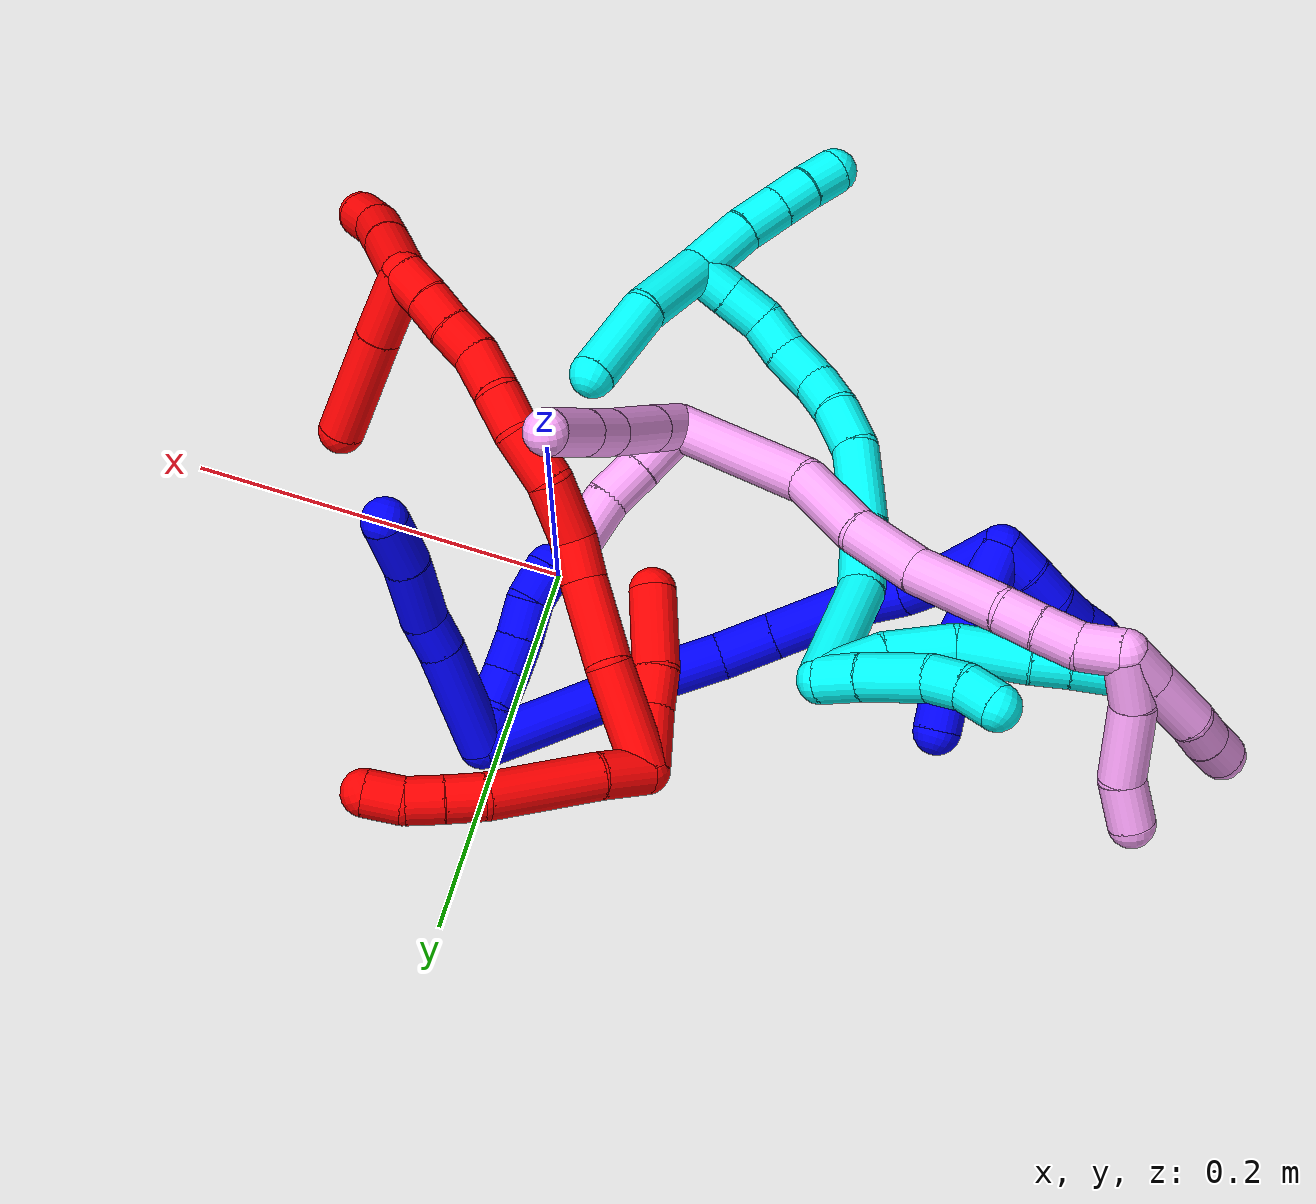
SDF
<sdf version="1.7">
 <world name="default">
  <plugin name="TubeGeneratorPlugin" filename="libtube_generator_plugin.so"/>
  <model name="photoneo_s_sensor">
   <static>1</static>
   <pose>0 0 2 1.57079 1.57079 3.14159</pose>
   <link name="link">
    <inertial><mass>0.1</mass></inertial>
    <sensor name="sensor" type="depth">
     <update_rate>30</update_rate>
     <camera>
      <horizontal_fov>1.22</horizontal_fov>
      <image><width>1920</width><height>1200</height><format>B8G8R8</format></image>
      <clip><near>0.1</near><far>4</far></clip>
      <depth_camera><output>points</output></depth_camera>
     </camera>
     <plugin name="camera_plugin" filename="libgazebo_ros_depth_camera.so">
      <baseline>0.2</baseline>
      <alwaysOn>1</alwaysOn>
      <updateRate>0.0</updateRate>
      <cameraName>camera_ir</cameraName>
      <imageTopicName>/camera/color/image_raw</imageTopicName>
      <cameraInfoTopicName>/camera/color/camera_info</cameraInfoTopicName>
      <depthImageTopicName>/camera/depth/image_raw</depthImageTopicName>
      <depthImageCameraInfoTopicName>/camera/depth/camera_info</depthImageCameraInfoTopicName>
      <pointCloudTopicName>/camera/depth/points</pointCloudTopicName>
      <frameName>fr_optical</frameName>
      <pointCloudCutoff>0.1</pointCloudCutoff>
      <pointCloudCutoffMax>2.0</pointCloudCutoffMax>
      <distortionK1>0</distortionK1>
      <distortionK2>0</distortionK2>
      <distortionK3>0</distortionK3>
      <distortionT1>0</distortionT1>
      <distortionT2>0</distortionT2>
      <CxPrime>0</CxPrime>
      <Cx>0</Cx>
      <Cy>0</Cy>
      <focalLength>0</focalLength>
      <hackBaseline>0</hackBaseline>
     </plugin>
    </sensor>
   </link>
  </model>
  <gravity>0 0 -9.8</gravity>
  <magnetic_field>6e-06 2.3e-05 -4.2e-05</magnetic_field>
  <atmosphere type="adiabatic"/>
  <physics name="default_physics" default="0" type="ode">
   <max_step_size>0.003</max_step_size>
   <real_time_factor>1</real_time_factor>
   <real_time_update_rate>1000</real_time_update_rate>
   <max_contacts>10000</max_contacts>
   <ode>
    <solver>
     <type>quick</type>
     <iters>100</iters>
     <sor>1.3</sor>
     <use_dynamic_moi_rescaling>0</use_dynamic_moi_rescaling>
    </solver>
    <constraints>
     <contact_max_correcting_vel>0</contact_max_correcting_vel>
     <contact_surface_layer>0.001</contact_surface_layer>
     <cfm>0</cfm>
     <erp>0.2</erp>
    </constraints>
   </ode>
  </physics>
  <scene><ambient>0.4 0.4 0.4 1</ambient><background>0.7 0.7 0.7 1</background><shadows>0</shadows></scene>
  <audio><device>default</device></audio>
  <spherical_coordinates>
   <surface_model>EARTH_WGS84</surface_model>
   <latitude_deg>0</latitude_deg>
   <longitude_deg>0</longitude_deg>
   <elevation>0</elevation>
   <heading_deg>0</heading_deg>
  </spherical_coordinates>
  <model name="bin">
   <static>1</static>
   <link name="bottom">
    <collision name="collision-bottom">
     <pose>0 0 -0.01 0 -0 0</pose>
     <geometry><box><size>0.8 0.6 0.02</size></box></geometry>
     <surface>
      <friction><ode><mu>100</mu><mu2>100</mu2></ode></friction>
      <contact><collide_bitmask>65535</collide_bitmask></contact>
     </surface>
    </collision>
   </link>
   <link name="west_wall">
    <collision name="collision-west_wall">
     <pose>-0.41 0 0.1 0 -0 0</pose>
     <geometry><box><size>0.02 0.6 0.2</size></box></geometry>
     <surface>
      <friction><ode><mu>100</mu><mu2>100</mu2></ode></friction>
      <contact><collide_bitmask>65535</collide_bitmask></contact>
     </surface>
    </collision>
   </link>
   <link name="east_wall">
    <collision name="collision-east_wall">
     <pose>0.41 0 0.1 0 -0 0</pose>
     <geometry><box><size>0.02 0.6 0.2</size></box></geometry>
     <surface>
      <friction><ode><mu>100</mu><mu2>100</mu2></ode></friction>
      <contact><collide_bitmask>65535</collide_bitmask></contact>
     </surface>
    </collision>
   </link>
   <link name="south_wall">
    <collision name="collision-south_wall">
     <pose>0 -0.31 0.1 0 -0 0</pose>
     <geometry><box><size>0.8 0.02 0.2</size></box></geometry>
     <surface>
      <friction><ode><mu>100</mu><mu2>100</mu2></ode></friction>
      <contact><collide_bitmask>65535</collide_bitmask></contact>
     </surface>
    </collision>
   </link>
   <link name="north_wall">
    <collision name="collision-north_wall">
     <pose>0 0.31 0.1 0 -0 0</pose>
     <geometry><box><size>0.8 0.02 0.2</size></box></geometry>
     <surface>
      <friction><ode><mu>100</mu><mu2>100</mu2></ode></friction>
      <contact><collide_bitmask>65535</collide_bitmask></contact>
     </surface>
    </collision>
   </link>
  </model>
  <model name="1">
   <static>0</static>
   <link name="1">
    <collision name="collision-cylinder-e_1_2_8">
     <pose>0.017224 -0.015923 -0.02046 2.48026 0.586411 1.44275</pose>
     <geometry><cylinder><radius>0.0125</radius><length>0.062251</length></cylinder></geometry>
     <surface>
      <friction><ode><mu>1.16</mu><mu2>1.16</mu2><slip1>0</slip1><slip2>0</slip2></ode></friction>
      <contact><ode><kp>1e+06</kp><kd>1</kd><max_vel>0</max_vel><min_depth>0.001</min_depth></ode></contact>
     </surface>
    </collision>
    <visual name="visual-cylinder-e_1_2_8">
     <pose>0.017224 -0.015923 -0.02046 2.48026 0.586411 1.44275</pose>
     <geometry><cylinder><radius>0.0125</radius><length>0.062251</length></cylinder></geometry>
     <material><ambient>0 0 1 1</ambient></material>
    </visual>
    <collision name="collision-cylinder-e_2_8_9">
     <pose>0.040623 -0.037073 -0.04688 2.42162 0.661681 1.47939</pose>
     <geometry><cylinder><radius>0.0125</radius><length>0.020097</length></cylinder></geometry>
     <surface>
      <friction><ode><mu>1.16</mu><mu2>1.16</mu2><slip1>0</slip1><slip2>0</slip2></ode></friction>
      <contact><ode><kp>1e+06</kp><kd>1</kd><max_vel>0</max_vel><min_depth>0.001</min_depth></ode></contact>
     </surface>
    </collision>
    <visual name="visual-cylinder-e_2_8_9">
     <pose>0.040623 -0.037073 -0.04688 2.42162 0.661681 1.47939</pose>
     <geometry><cylinder><radius>0.0125</radius><length>0.020097</length></cylinder></geometry>
     <material><ambient>0 0 1 1</ambient></material>
    </visual>
    <collision name="collision-cylinder-e_3_9_10">
     <pose>0.054578 -0.054988 -0.064205 2.30125 0.428535 0.906482</pose>
     <geometry><cylinder><radius>0.0125</radius><length>0.037453</length></cylinder></geometry>
     <surface>
      <friction><ode><mu>1.16</mu><mu2>1.16</mu2><slip1>0</slip1><slip2>0</slip2></ode></friction>
      <contact><ode><kp>1e+06</kp><kd>1</kd><max_vel>0</max_vel><min_depth>0.001</min_depth></ode></contact>
     </surface>
    </collision>
    <visual name="visual-cylinder-e_3_9_10">
     <pose>0.054578 -0.054988 -0.064205 2.30125 0.428535 0.906482</pose>
     <geometry><cylinder><radius>0.0125</radius><length>0.037453</length></cylinder></geometry>
     <material><ambient>0 0 1 1</ambient></material>
    </visual>
    <collision name="collision-cylinder-e_4_10_6">
     <pose>0.070152 -0.077727 -0.083708 2.25139 0.542261 1.05524</pose>
     <geometry><cylinder><radius>0.0125</radius><length>0.030199</length></cylinder></geometry>
     <surface>
      <friction><ode><mu>1.16</mu><mu2>1.16</mu2><slip1>0</slip1><slip2>0</slip2></ode></friction>
      <contact><ode><kp>1e+06</kp><kd>1</kd><max_vel>0</max_vel><min_depth>0.001</min_depth></ode></contact>
     </surface>
    </collision>
    <visual name="visual-cylinder-e_4_10_6">
     <pose>0.070152 -0.077727 -0.083708 2.25139 0.542261 1.05524</pose>
     <geometry><cylinder><radius>0.0125</radius><length>0.030199</length></cylinder></geometry>
     <material><ambient>0 0 1 1</ambient></material>
    </visual>
    <collision name="collision-cylinder-e_1_2_11">
     <pose>0.000467 1.9e-05 -0.009989 -3.13973 0.046678 -3.06166</pose>
     <geometry><cylinder><radius>0.0125</radius><length>0.02</length></cylinder></geometry>
     <surface>
      <friction><ode><mu>1.16</mu><mu2>1.16</mu2><slip1>0</slip1><slip2>0</slip2></ode></friction>
      <contact><ode><kp>1e+06</kp><kd>1</kd><max_vel>0</max_vel><min_depth>0.001</min_depth></ode></contact>
     </surface>
    </collision>
    <visual name="visual-cylinder-e_1_2_11">
     <pose>0.000467 1.9e-05 -0.009989 -3.13973 0.046678 -3.06166</pose>
     <geometry><cylinder><radius>0.0125</radius><length>0.02</length></cylinder></geometry>
     <material><ambient>0 0 1 1</ambient></material>
    </visual>
    <collision name="collision-cylinder-e_2_11_12">
     <pose>0.00012 0.002776 -0.029561 -2.8632 -0.081403 0.565758</pose>
     <geometry><cylinder><radius>0.0125</radius><length>0.02</length></cylinder></geometry>
     <surface>
      <friction><ode><mu>1.16</mu><mu2>1.16</mu2><slip1>0</slip1><slip2>0</slip2></ode></friction>
      <contact><ode><kp>1e+06</kp><kd>1</kd><max_vel>0</max_vel><min_depth>0.001</min_depth></ode></contact>
     </surface>
    </collision>
    <visual name="visual-cylinder-e_2_11_12">
     <pose>0.00012 0.002776 -0.029561 -2.8632 -0.081403 0.565758</pose>
     <geometry><cylinder><radius>0.0125</radius><length>0.02</length></cylinder></geometry>
     <material><ambient>0 0 1 1</ambient></material>
    </visual>
    <collision name="collision-cylinder-e_3_12_13">
     <pose>-0.001257 0.00519 -0.049123 3.109 -0.056398 -2.09361</pose>
     <geometry><cylinder><radius>0.0125</radius><length>0.02</length></cylinder></geometry>
     <surface>
      <friction><ode><mu>1.16</mu><mu2>1.16</mu2><slip1>0</slip1><slip2>0</slip2></ode></friction>
      <contact><ode><kp>1e+06</kp><kd>1</kd><max_vel>0</max_vel><min_depth>0.001</min_depth></ode></contact>
     </surface>
    </collision>
    <visual name="visual-cylinder-e_3_12_13">
     <pose>-0.001257 0.00519 -0.049123 3.109 -0.056398 -2.09361</pose>
     <geometry><cylinder><radius>0.0125</radius><length>0.02</length></cylinder></geometry>
     <material><ambient>0 0 1 1</ambient></material>
    </visual>
    <collision name="collision-cylinder-e_4_13_14">
     <pose>-0.00156 0.004227 -0.069078 3.07776 0.026017 0.77389</pose>
     <geometry><cylinder><radius>0.0125</radius><length>0.02</length></cylinder></geometry>
     <surface>
      <friction><ode><mu>1.16</mu><mu2>1.16</mu2><slip1>0</slip1><slip2>0</slip2></ode></friction>
      <contact><ode><kp>1e+06</kp><kd>1</kd><max_vel>0</max_vel><min_depth>0.001</min_depth></ode></contact>
     </surface>
    </collision>
    <visual name="visual-cylinder-e_4_13_14">
     <pose>-0.00156 0.004227 -0.069078 3.07776 0.026017 0.77389</pose>
     <geometry><cylinder><radius>0.0125</radius><length>0.02</length></cylinder></geometry>
     <material><ambient>0 0 1 1</ambient></material>
    </visual>
    <collision name="collision-cylinder-e_5_14_5">
     <pose>-0.003602 0.004286 -0.088761 -3.06998 -0.232297 2.54582</pose>
     <geometry><cylinder><radius>0.0125</radius><length>0.02</length></cylinder></geometry>
     <surface>
      <friction><ode><mu>1.16</mu><mu2>1.16</mu2><slip1>0</slip1><slip2>0</slip2></ode></friction>
      <contact><ode><kp>1e+06</kp><kd>1</kd><max_vel>0</max_vel><min_depth>0.001</min_depth></ode></contact>
     </surface>
    </collision>
    <visual name="visual-cylinder-e_5_14_5">
     <pose>-0.003602 0.004286 -0.088761 -3.06998 -0.232297 2.54582</pose>
     <geometry><cylinder><radius>0.0125</radius><length>0.02</length></cylinder></geometry>
     <material><ambient>0 0 1 1</ambient></material>
    </visual>
    <collision name="collision-cylinder-e_1_2_15">
     <pose>-0.040001 0.006552 -0.031593 -2.9371 -0.892038 2.71884</pose>
     <geometry><cylinder><radius>0.0125</radius><length>0.102783</length></cylinder></geometry>
     <surface>
      <friction><ode><mu>1.16</mu><mu2>1.16</mu2><slip1>0</slip1><slip2>0</slip2></ode></friction>
      <contact><ode><kp>1e+06</kp><kd>1</kd><max_vel>0</max_vel><min_depth>0.001</min_depth></ode></contact>
     </surface>
    </collision>
    <visual name="visual-cylinder-e_1_2_15">
     <pose>-0.040001 0.006552 -0.031593 -2.9371 -0.892038 2.71884</pose>
     <geometry><cylinder><radius>0.0125</radius><length>0.102783</length></cylinder></geometry>
     <material><ambient>0 0 1 1</ambient></material>
    </visual>
    <collision name="collision-cylinder-e_2_15_16">
     <pose>-0.092533 0.014156 -0.072145 -3.02467 -0.946836 2.91408</pose>
     <geometry><cylinder><radius>0.0125</radius><length>0.030881</length></cylinder></geometry>
     <surface>
      <friction><ode><mu>1.16</mu><mu2>1.16</mu2><slip1>0</slip1><slip2>0</slip2></ode></friction>
      <contact><ode><kp>1e+06</kp><kd>1</kd><max_vel>0</max_vel><min_depth>0.001</min_depth></ode></contact>
     </surface>
    </collision>
    <visual name="visual-cylinder-e_2_15_16">
     <pose>-0.092533 0.014156 -0.072145 -3.02467 -0.946836 2.91408</pose>
     <geometry><cylinder><radius>0.0125</radius><length>0.030881</length></cylinder></geometry>
     <material><ambient>0 0 1 1</ambient></material>
    </visual>
    <collision name="collision-cylinder-e_3_16_17">
     <pose>-0.116734 0.012856 -0.090287 2.89082 -0.888638 -2.62393</pose>
     <geometry><cylinder><radius>0.0125</radius><length>0.03007</length></cylinder></geometry>
     <surface>
      <friction><ode><mu>1.16</mu><mu2>1.16</mu2><slip1>0</slip1><slip2>0</slip2></ode></friction>
      <contact><ode><kp>1e+06</kp><kd>1</kd><max_vel>0</max_vel><min_depth>0.001</min_depth></ode></contact>
     </surface>
    </collision>
    <visual name="visual-cylinder-e_3_16_17">
     <pose>-0.116734 0.012856 -0.090287 2.89082 -0.888638 -2.62393</pose>
     <geometry><cylinder><radius>0.0125</radius><length>0.03007</length></cylinder></geometry>
     <material><ambient>0 0 1 1</ambient></material>
    </visual>
    <collision name="collision-cylinder-e_4_17_18">
     <pose>-0.147884 0.006396 -0.114829 2.88023 -0.886242 -2.60128</pose>
     <geometry><cylinder><radius>0.0125</radius><length>0.050288</length></cylinder></geometry>
     <surface>
      <friction><ode><mu>1.16</mu><mu2>1.16</mu2><slip1>0</slip1><slip2>0</slip2></ode></friction>
      <contact><ode><kp>1e+06</kp><kd>1</kd><max_vel>0</max_vel><min_depth>0.001</min_depth></ode></contact>
     </surface>
    </collision>
    <visual name="visual-cylinder-e_4_17_18">
     <pose>-0.147884 0.006396 -0.114829 2.88023 -0.886242 -2.60128</pose>
     <geometry><cylinder><radius>0.0125</radius><length>0.050288</length></cylinder></geometry>
     <material><ambient>0 0 1 1</ambient></material>
    </visual>
    <collision name="collision-cylinder-e_5_18_19">
     <pose>-0.176978 -0.001322 -0.135533 2.54764 -0.979974 -2.09979</pose>
     <geometry><cylinder><radius>0.0125</radius><length>0.023155</length></cylinder></geometry>
     <surface>
      <friction><ode><mu>1.16</mu><mu2>1.16</mu2><slip1>0</slip1><slip2>0</slip2></ode></friction>
      <contact><ode><kp>1e+06</kp><kd>1</kd><max_vel>0</max_vel><min_depth>0.001</min_depth></ode></contact>
     </surface>
    </collision>
    <visual name="visual-cylinder-e_5_18_19">
     <pose>-0.176978 -0.001322 -0.135533 2.54764 -0.979974 -2.09979</pose>
     <geometry><cylinder><radius>0.0125</radius><length>0.023155</length></cylinder></geometry>
     <material><ambient>0 0 1 1</ambient></material>
    </visual>
    <collision name="collision-cylinder-e_6_19_20">
     <pose>-0.195944 -0.013294 -0.147816 2.26331 -0.710614 -1.33714</pose>
     <geometry><cylinder><radius>0.0125</radius><length>0.028672</length></cylinder></geometry>
     <surface>
      <friction><ode><mu>1.16</mu><mu2>1.16</mu2><slip1>0</slip1><slip2>0</slip2></ode></friction>
      <contact><ode><kp>1e+06</kp><kd>1</kd><max_vel>0</max_vel><min_depth>0.001</min_depth></ode></contact>
     </surface>
    </collision>
    <visual name="visual-cylinder-e_6_19_20">
     <pose>-0.195944 -0.013294 -0.147816 2.26331 -0.710614 -1.33714</pose>
     <geometry><cylinder><radius>0.0125</radius><length>0.028672</length></cylinder></geometry>
     <material><ambient>0 0 1 1</ambient></material>
    </visual>
    <collision name="collision-cylinder-e_7_20_1">
     <pose>-0.214786 -0.032113 -0.164354 2.31354 -0.589336 -1.20888</pose>
     <geometry><cylinder><radius>0.0125</radius><length>0.034151</length></cylinder></geometry>
     <surface>
      <friction><ode><mu>1.16</mu><mu2>1.16</mu2><slip1>0</slip1><slip2>0</slip2></ode></friction>
      <contact><ode><kp>1e+06</kp><kd>1</kd><max_vel>0</max_vel><min_depth>0.001</min_depth></ode></contact>
     </surface>
    </collision>
    <visual name="visual-cylinder-e_7_20_1">
     <pose>-0.214786 -0.032113 -0.164354 2.31354 -0.589336 -1.20888</pose>
     <geometry><cylinder><radius>0.0125</radius><length>0.034151</length></cylinder></geometry>
     <material><ambient>0 0 1 1</ambient></material>
    </visual>
    <collision name="collision-cylinder-e_1_1_21">
     <pose>-0.23303 -0.040109 -0.169793 -0.534054 -1.06624 0.320104</pose>
     <geometry><cylinder><radius>0.0125</radius><length>0.02</length></cylinder></geometry>
     <surface>
      <friction><ode><mu>1.16</mu><mu2>1.16</mu2><slip1>0</slip1><slip2>0</slip2></ode></friction>
      <contact><ode><kp>1e+06</kp><kd>1</kd><max_vel>0</max_vel><min_depth>0.001</min_depth></ode></contact>
     </surface>
    </collision>
    <visual name="visual-cylinder-e_1_1_21">
     <pose>-0.23303 -0.040109 -0.169793 -0.534054 -1.06624 0.320104</pose>
     <geometry><cylinder><radius>0.0125</radius><length>0.02</length></cylinder></geometry>
     <material><ambient>0 0 1 1</ambient></material>
    </visual>
    <collision name="collision-cylinder-e_2_21_22">
     <pose>-0.249985 -0.033951 -0.161263 -0.702306 -0.961472 0.377571</pose>
     <geometry><cylinder><radius>0.0125</radius><length>0.02</length></cylinder></geometry>
     <surface>
      <friction><ode><mu>1.16</mu><mu2>1.16</mu2><slip1>0</slip1><slip2>0</slip2></ode></friction>
      <contact><ode><kp>1e+06</kp><kd>1</kd><max_vel>0</max_vel><min_depth>0.001</min_depth></ode></contact>
     </surface>
    </collision>
    <visual name="visual-cylinder-e_2_21_22">
     <pose>-0.249985 -0.033951 -0.161263 -0.702306 -0.961472 0.377571</pose>
     <geometry><cylinder><radius>0.0125</radius><length>0.02</length></cylinder></geometry>
     <material><ambient>0 0 1 1</ambient></material>
    </visual>
    <collision name="collision-cylinder-e_3_22_23">
     <pose>-0.265518 -0.024067 -0.154075 -1.14324 -0.823216 0.547517</pose>
     <geometry><cylinder><radius>0.0125</radius><length>0.02</length></cylinder></geometry>
     <surface>
      <friction><ode><mu>1.16</mu><mu2>1.16</mu2><slip1>0</slip1><slip2>0</slip2></ode></friction>
      <contact><ode><kp>1e+06</kp><kd>1</kd><max_vel>0</max_vel><min_depth>0.001</min_depth></ode></contact>
     </surface>
    </collision>
    <visual name="visual-cylinder-e_3_22_23">
     <pose>-0.265518 -0.024067 -0.154075 -1.14324 -0.823216 0.547517</pose>
     <geometry><cylinder><radius>0.0125</radius><length>0.02</length></cylinder></geometry>
     <material><ambient>0 0 1 1</ambient></material>
    </visual>
    <collision name="collision-cylinder-e_4_23_24">
     <pose>-0.280194 -0.011301 -0.149584 -1.32197 -0.824542 0.655668</pose>
     <geometry><cylinder><radius>0.0125</radius><length>0.02</length></cylinder></geometry>
     <surface>
      <friction><ode><mu>1.16</mu><mu2>1.16</mu2><slip1>0</slip1><slip2>0</slip2></ode></friction>
      <contact><ode><kp>1e+06</kp><kd>1</kd><max_vel>0</max_vel><min_depth>0.001</min_depth></ode></contact>
     </surface>
    </collision>
    <visual name="visual-cylinder-e_4_23_24">
     <pose>-0.280194 -0.011301 -0.149584 -1.32197 -0.824542 0.655668</pose>
     <geometry><cylinder><radius>0.0125</radius><length>0.02</length></cylinder></geometry>
     <material><ambient>0 0 1 1</ambient></material>
    </visual>
    <collision name="collision-cylinder-e_5_24_4">
     <pose>-0.294081 0.00216 -0.144777 -1.1433 -0.713439 0.470585</pose>
     <geometry><cylinder><radius>0.0125</radius><length>0.02</length></cylinder></geometry>
     <surface>
      <friction><ode><mu>1.16</mu><mu2>1.16</mu2><slip1>0</slip1><slip2>0</slip2></ode></friction>
      <contact><ode><kp>1e+06</kp><kd>1</kd><max_vel>0</max_vel><min_depth>0.001</min_depth></ode></contact>
     </surface>
    </collision>
    <visual name="visual-cylinder-e_5_24_4">
     <pose>-0.294081 0.00216 -0.144777 -1.1433 -0.713439 0.470585</pose>
     <geometry><cylinder><radius>0.0125</radius><length>0.02</length></cylinder></geometry>
     <material><ambient>0 0 1 1</ambient></material>
    </visual>
    <collision name="collision-cylinder-e_1_1_25">
     <pose>-0.222964 -0.043929 -0.160852 0.103368 0.099318 0.005142</pose>
     <geometry><cylinder><radius>0.0125</radius><length>0.026475</length></cylinder></geometry>
     <surface>
      <friction><ode><mu>1.16</mu><mu2>1.16</mu2><slip1>0</slip1><slip2>0</slip2></ode></friction>
      <contact><ode><kp>1e+06</kp><kd>1</kd><max_vel>0</max_vel><min_depth>0.001</min_depth></ode></contact>
     </surface>
    </collision>
    <visual name="visual-cylinder-e_1_1_25">
     <pose>-0.222964 -0.043929 -0.160852 0.103368 0.099318 0.005142</pose>
     <geometry><cylinder><radius>0.0125</radius><length>0.026475</length></cylinder></geometry>
     <material><ambient>0 0 1 1</ambient></material>
    </visual>
    <collision name="collision-cylinder-e_2_25_26">
     <pose>-0.218836 -0.046042 -0.13191 0.047601 0.175721 0.004194</pose>
     <geometry><cylinder><radius>0.0125</radius><length>0.032211</length></cylinder></geometry>
     <surface>
      <friction><ode><mu>1.16</mu><mu2>1.16</mu2><slip1>0</slip1><slip2>0</slip2></ode></friction>
      <contact><ode><kp>1e+06</kp><kd>1</kd><max_vel>0</max_vel><min_depth>0.001</min_depth></ode></contact>
     </surface>
    </collision>
    <visual name="visual-cylinder-e_2_25_26">
     <pose>-0.218836 -0.046042 -0.13191 0.047601 0.175721 0.004194</pose>
     <geometry><cylinder><radius>0.0125</radius><length>0.032211</length></cylinder></geometry>
     <material><ambient>0 0 1 1</ambient></material>
    </visual>
    <collision name="collision-cylinder-e_3_26_3">
     <pose>-0.21771 -0.046513 -0.095485 -0.013802 -0.081884 0.000565</pose>
     <geometry><cylinder><radius>0.0125</radius><length>0.041314</length></cylinder></geometry>
     <surface>
      <friction><ode><mu>1.16</mu><mu2>1.16</mu2><slip1>0</slip1><slip2>0</slip2></ode></friction>
      <contact><ode><kp>1e+06</kp><kd>1</kd><max_vel>0</max_vel><min_depth>0.001</min_depth></ode></contact>
     </surface>
    </collision>
    <visual name="visual-cylinder-e_3_26_3">
     <pose>-0.21771 -0.046513 -0.095485 -0.013802 -0.081884 0.000565</pose>
     <geometry><cylinder><radius>0.0125</radius><length>0.041314</length></cylinder></geometry>
     <material><ambient>0 0 1 1</ambient></material>
    </visual>
    <collision name="collision-sphere-3">
     <pose>-0.219399 -0.046229 -0.074899 0 -0 0</pose>
     <geometry><sphere><radius>0.0125</radius></sphere></geometry>
     <surface>
      <friction><ode><mu>1.16</mu><mu2>1.16</mu2><slip1>0</slip1><slip2>0</slip2></ode></friction>
      <contact><ode><kp>1e+06</kp><kd>1</kd><max_vel>0</max_vel><min_depth>0.001</min_depth></ode></contact>
     </surface>
    </collision>
    <visual name="visual-sphere-3">
     <pose>-0.219399 -0.046229 -0.074899 0 -0 0</pose>
     <geometry><sphere><radius>0.0125</radius></sphere></geometry>
     <material><ambient>0 0 1 1</ambient></material>
    </visual>
    <collision name="collision-sphere-26">
     <pose>-0.21602 -0.046797 -0.116071 0 -0 0</pose>
     <geometry><sphere><radius>0.0125</radius></sphere></geometry>
     <surface>
      <friction><ode><mu>1.16</mu><mu2>1.16</mu2><slip1>0</slip1><slip2>0</slip2></ode></friction>
      <contact><ode><kp>1e+06</kp><kd>1</kd><max_vel>0</max_vel><min_depth>0.001</min_depth></ode></contact>
     </surface>
    </collision>
    <visual name="visual-sphere-26">
     <pose>-0.21602 -0.046797 -0.116071 0 -0 0</pose>
     <geometry><sphere><radius>0.0125</radius></sphere></geometry>
     <material><ambient>0 0 1 1</ambient></material>
    </visual>
    <collision name="collision-sphere-25">
     <pose>-0.221651 -0.045288 -0.14775 0 -0 0</pose>
     <geometry><sphere><radius>0.0125</radius></sphere></geometry>
     <surface>
      <friction><ode><mu>1.16</mu><mu2>1.16</mu2><slip1>0</slip1><slip2>0</slip2></ode></friction>
      <contact><ode><kp>1e+06</kp><kd>1</kd><max_vel>0</max_vel><min_depth>0.001</min_depth></ode></contact>
     </surface>
    </collision>
    <visual name="visual-sphere-25">
     <pose>-0.221651 -0.045288 -0.14775 0 -0 0</pose>
     <geometry><sphere><radius>0.0125</radius></sphere></geometry>
     <material><ambient>0 0 1 1</ambient></material>
    </visual>
    <collision name="collision-sphere-4">
     <pose>-0.300625 0.00904 -0.141643 0 -0 0</pose>
     <geometry><sphere><radius>0.0125</radius></sphere></geometry>
     <surface>
      <friction><ode><mu>1.16</mu><mu2>1.16</mu2><slip1>0</slip1><slip2>0</slip2></ode></friction>
      <contact><ode><kp>1e+06</kp><kd>1</kd><max_vel>0</max_vel><min_depth>0.001</min_depth></ode></contact>
     </surface>
    </collision>
    <visual name="visual-sphere-4">
     <pose>-0.300625 0.00904 -0.141643 0 -0 0</pose>
     <geometry><sphere><radius>0.0125</radius></sphere></geometry>
     <material><ambient>0 0 1 1</ambient></material>
    </visual>
    <collision name="collision-sphere-24">
     <pose>-0.287536 -0.004721 -0.147912 0 -0 0</pose>
     <geometry><sphere><radius>0.0125</radius></sphere></geometry>
     <surface>
      <friction><ode><mu>1.16</mu><mu2>1.16</mu2><slip1>0</slip1><slip2>0</slip2></ode></friction>
      <contact><ode><kp>1e+06</kp><kd>1</kd><max_vel>0</max_vel><min_depth>0.001</min_depth></ode></contact>
     </surface>
    </collision>
    <visual name="visual-sphere-24">
     <pose>-0.287536 -0.004721 -0.147912 0 -0 0</pose>
     <geometry><sphere><radius>0.0125</radius></sphere></geometry>
     <material><ambient>0 0 1 1</ambient></material>
    </visual>
    <collision name="collision-sphere-23">
     <pose>-0.272852 -0.017881 -0.151256 0 -0 0</pose>
     <geometry><sphere><radius>0.0125</radius></sphere></geometry>
     <surface>
      <friction><ode><mu>1.16</mu><mu2>1.16</mu2><slip1>0</slip1><slip2>0</slip2></ode></friction>
      <contact><ode><kp>1e+06</kp><kd>1</kd><max_vel>0</max_vel><min_depth>0.001</min_depth></ode></contact>
     </surface>
    </collision>
    <visual name="visual-sphere-23">
     <pose>-0.272852 -0.017881 -0.151256 0 -0 0</pose>
     <geometry><sphere><radius>0.0125</radius></sphere></geometry>
     <material><ambient>0 0 1 1</ambient></material>
    </visual>
    <collision name="collision-sphere-22">
     <pose>-0.258185 -0.030254 -0.156894 0 -0 0</pose>
     <geometry><sphere><radius>0.0125</radius></sphere></geometry>
     <surface>
      <friction><ode><mu>1.16</mu><mu2>1.16</mu2><slip1>0</slip1><slip2>0</slip2></ode></friction>
      <contact><ode><kp>1e+06</kp><kd>1</kd><max_vel>0</max_vel><min_depth>0.001</min_depth></ode></contact>
     </surface>
    </collision>
    <visual name="visual-sphere-22">
     <pose>-0.258185 -0.030254 -0.156894 0 -0 0</pose>
     <geometry><sphere><radius>0.0125</radius></sphere></geometry>
     <material><ambient>0 0 1 1</ambient></material>
    </visual>
    <collision name="collision-sphere-21">
     <pose>-0.241784 -0.037648 -0.165632 0 -0 0</pose>
     <geometry><sphere><radius>0.0125</radius></sphere></geometry>
     <surface>
      <friction><ode><mu>1.16</mu><mu2>1.16</mu2><slip1>0</slip1><slip2>0</slip2></ode></friction>
      <contact><ode><kp>1e+06</kp><kd>1</kd><max_vel>0</max_vel><min_depth>0.001</min_depth></ode></contact>
     </surface>
    </collision>
    <visual name="visual-sphere-21">
     <pose>-0.241784 -0.037648 -0.165632 0 -0 0</pose>
     <geometry><sphere><radius>0.0125</radius></sphere></geometry>
     <material><ambient>0 0 1 1</ambient></material>
    </visual>
    <collision name="collision-sphere-1">
     <pose>-0.224276 -0.04257 -0.173954 0 -0 0</pose>
     <geometry><sphere><radius>0.0125</radius></sphere></geometry>
     <surface>
      <friction><ode><mu>1.16</mu><mu2>1.16</mu2><slip1>0</slip1><slip2>0</slip2></ode></friction>
      <contact><ode><kp>1e+06</kp><kd>1</kd><max_vel>0</max_vel><min_depth>0.001</min_depth></ode></contact>
     </surface>
    </collision>
    <visual name="visual-sphere-1">
     <pose>-0.224276 -0.04257 -0.173954 0 -0 0</pose>
     <geometry><sphere><radius>0.0125</radius></sphere></geometry>
     <material><ambient>0 0 1 1</ambient></material>
    </visual>
    <collision name="collision-sphere-11">
     <pose>0.000933 3.7e-05 -0.019978 0 -0 0</pose>
     <geometry><sphere><radius>0.0125</radius></sphere></geometry>
     <surface>
      <friction><ode><mu>1.16</mu><mu2>1.16</mu2><slip1>0</slip1><slip2>0</slip2></ode></friction>
      <contact><ode><kp>1e+06</kp><kd>1</kd><max_vel>0</max_vel><min_depth>0.001</min_depth></ode></contact>
     </surface>
    </collision>
    <visual name="visual-sphere-11">
     <pose>0.000933 3.7e-05 -0.019978 0 -0 0</pose>
     <geometry><sphere><radius>0.0125</radius></sphere></geometry>
     <material><ambient>0 0 1 1</ambient></material>
    </visual>
    <collision name="collision-sphere-6">
     <pose>0.077945 -0.087779 -0.091846 0 -0 0</pose>
     <geometry><sphere><radius>0.0125</radius></sphere></geometry>
     <surface>
      <friction><ode><mu>1.16</mu><mu2>1.16</mu2><slip1>0</slip1><slip2>0</slip2></ode></friction>
      <contact><ode><kp>1e+06</kp><kd>1</kd><max_vel>0</max_vel><min_depth>0.001</min_depth></ode></contact>
     </surface>
    </collision>
    <visual name="visual-sphere-6">
     <pose>0.077945 -0.087779 -0.091846 0 -0 0</pose>
     <geometry><sphere><radius>0.0125</radius></sphere></geometry>
     <material><ambient>0 0 1 1</ambient></material>
    </visual>
    <collision name="collision-sphere-10">
     <pose>0.06236 -0.067675 -0.07557 0 -0 0</pose>
     <geometry><sphere><radius>0.0125</radius></sphere></geometry>
     <surface>
      <friction><ode><mu>1.16</mu><mu2>1.16</mu2><slip1>0</slip1><slip2>0</slip2></ode></friction>
      <contact><ode><kp>1e+06</kp><kd>1</kd><max_vel>0</max_vel><min_depth>0.001</min_depth></ode></contact>
     </surface>
    </collision>
    <visual name="visual-sphere-10">
     <pose>0.06236 -0.067675 -0.07557 0 -0 0</pose>
     <geometry><sphere><radius>0.0125</radius></sphere></geometry>
     <material><ambient>0 0 1 1</ambient></material>
    </visual>
    <collision name="collision-sphere-9">
     <pose>0.046797 -0.0423 -0.05284 0 -0 0</pose>
     <geometry><sphere><radius>0.0125</radius></sphere></geometry>
     <surface>
      <friction><ode><mu>1.16</mu><mu2>1.16</mu2><slip1>0</slip1><slip2>0</slip2></ode></friction>
      <contact><ode><kp>1e+06</kp><kd>1</kd><max_vel>0</max_vel><min_depth>0.001</min_depth></ode></contact>
     </surface>
    </collision>
    <visual name="visual-sphere-9">
     <pose>0.046797 -0.0423 -0.05284 0 -0 0</pose>
     <geometry><sphere><radius>0.0125</radius></sphere></geometry>
     <material><ambient>0 0 1 1</ambient></material>
    </visual>
    <collision name="collision-sphere-2">
     <geometry><sphere><radius>0.0125</radius></sphere></geometry>
     <surface>
      <friction><ode><mu>1.16</mu><mu2>1.16</mu2><slip1>0</slip1><slip2>0</slip2></ode></friction>
      <contact><ode><kp>1e+06</kp><kd>1</kd><max_vel>0</max_vel><min_depth>0.001</min_depth></ode></contact>
     </surface>
    </collision>
    <visual name="visual-sphere-2">
     <geometry><sphere><radius>0.0125</radius></sphere></geometry>
     <material><ambient>0 0 1 1</ambient></material>
    </visual>
    <collision name="collision-sphere-19">
     <pose>-0.186592 -0.004931 -0.140878 0 -0 0</pose>
     <geometry><sphere><radius>0.0125</radius></sphere></geometry>
     <surface>
      <friction><ode><mu>1.16</mu><mu2>1.16</mu2><slip1>0</slip1><slip2>0</slip2></ode></friction>
      <contact><ode><kp>1e+06</kp><kd>1</kd><max_vel>0</max_vel><min_depth>0.001</min_depth></ode></contact>
     </surface>
    </collision>
    <visual name="visual-sphere-19">
     <pose>-0.186592 -0.004931 -0.140878 0 -0 0</pose>
     <geometry><sphere><radius>0.0125</radius></sphere></geometry>
     <material><ambient>0 0 1 1</ambient></material>
    </visual>
    <collision name="collision-sphere-8">
     <pose>0.034448 -0.031845 -0.04092 0 -0 0</pose>
     <geometry><sphere><radius>0.0125</radius></sphere></geometry>
     <surface>
      <friction><ode><mu>1.16</mu><mu2>1.16</mu2><slip1>0</slip1><slip2>0</slip2></ode></friction>
      <contact><ode><kp>1e+06</kp><kd>1</kd><max_vel>0</max_vel><min_depth>0.001</min_depth></ode></contact>
     </surface>
    </collision>
    <visual name="visual-sphere-8">
     <pose>0.034448 -0.031845 -0.04092 0 -0 0</pose>
     <geometry><sphere><radius>0.0125</radius></sphere></geometry>
     <material><ambient>0 0 1 1</ambient></material>
    </visual>
    <collision name="collision-sphere-12">
     <pose>-0.000693 0.005515 -0.039144 0 -0 0</pose>
     <geometry><sphere><radius>0.0125</radius></sphere></geometry>
     <surface>
      <friction><ode><mu>1.16</mu><mu2>1.16</mu2><slip1>0</slip1><slip2>0</slip2></ode></friction>
      <contact><ode><kp>1e+06</kp><kd>1</kd><max_vel>0</max_vel><min_depth>0.001</min_depth></ode></contact>
     </surface>
    </collision>
    <visual name="visual-sphere-12">
     <pose>-0.000693 0.005515 -0.039144 0 -0 0</pose>
     <geometry><sphere><radius>0.0125</radius></sphere></geometry>
     <material><ambient>0 0 1 1</ambient></material>
    </visual>
    <collision name="collision-sphere-13">
     <pose>-0.00182 0.004865 -0.059102 0 -0 0</pose>
     <geometry><sphere><radius>0.0125</radius></sphere></geometry>
     <surface>
      <friction><ode><mu>1.16</mu><mu2>1.16</mu2><slip1>0</slip1><slip2>0</slip2></ode></friction>
      <contact><ode><kp>1e+06</kp><kd>1</kd><max_vel>0</max_vel><min_depth>0.001</min_depth></ode></contact>
     </surface>
    </collision>
    <visual name="visual-sphere-13">
     <pose>-0.00182 0.004865 -0.059102 0 -0 0</pose>
     <geometry><sphere><radius>0.0125</radius></sphere></geometry>
     <material><ambient>0 0 1 1</ambient></material>
    </visual>
    <collision name="collision-sphere-14">
     <pose>-0.0013 0.003589 -0.079055 0 -0 0</pose>
     <geometry><sphere><radius>0.0125</radius></sphere></geometry>
     <surface>
      <friction><ode><mu>1.16</mu><mu2>1.16</mu2><slip1>0</slip1><slip2>0</slip2></ode></friction>
      <contact><ode><kp>1e+06</kp><kd>1</kd><max_vel>0</max_vel><min_depth>0.001</min_depth></ode></contact>
     </surface>
    </collision>
    <visual name="visual-sphere-14">
     <pose>-0.0013 0.003589 -0.079055 0 -0 0</pose>
     <geometry><sphere><radius>0.0125</radius></sphere></geometry>
     <material><ambient>0 0 1 1</ambient></material>
    </visual>
    <collision name="collision-sphere-5">
     <pose>-0.005904 0.004982 -0.098467 0 -0 0</pose>
     <geometry><sphere><radius>0.0125</radius></sphere></geometry>
     <surface>
      <friction><ode><mu>1.16</mu><mu2>1.16</mu2><slip1>0</slip1><slip2>0</slip2></ode></friction>
      <contact><ode><kp>1e+06</kp><kd>1</kd><max_vel>0</max_vel><min_depth>0.001</min_depth></ode></contact>
     </surface>
    </collision>
    <visual name="visual-sphere-5">
     <pose>-0.005904 0.004982 -0.098467 0 -0 0</pose>
     <geometry><sphere><radius>0.0125</radius></sphere></geometry>
     <material><ambient>0 0 1 1</ambient></material>
    </visual>
    <collision name="collision-sphere-15">
     <pose>-0.080001 0.013104 -0.063185 0 -0 0</pose>
     <geometry><sphere><radius>0.0125</radius></sphere></geometry>
     <surface>
      <friction><ode><mu>1.16</mu><mu2>1.16</mu2><slip1>0</slip1><slip2>0</slip2></ode></friction>
      <contact><ode><kp>1e+06</kp><kd>1</kd><max_vel>0</max_vel><min_depth>0.001</min_depth></ode></contact>
     </surface>
    </collision>
    <visual name="visual-sphere-15">
     <pose>-0.080001 0.013104 -0.063185 0 -0 0</pose>
     <geometry><sphere><radius>0.0125</radius></sphere></geometry>
     <material><ambient>0 0 1 1</ambient></material>
    </visual>
    <collision name="collision-sphere-16">
     <pose>-0.105064 0.015209 -0.081105 0 -0 0</pose>
     <geometry><sphere><radius>0.0125</radius></sphere></geometry>
     <surface>
      <friction><ode><mu>1.16</mu><mu2>1.16</mu2><slip1>0</slip1><slip2>0</slip2></ode></friction>
      <contact><ode><kp>1e+06</kp><kd>1</kd><max_vel>0</max_vel><min_depth>0.001</min_depth></ode></contact>
     </surface>
    </collision>
    <visual name="visual-sphere-16">
     <pose>-0.105064 0.015209 -0.081105 0 -0 0</pose>
     <geometry><sphere><radius>0.0125</radius></sphere></geometry>
     <material><ambient>0 0 1 1</ambient></material>
    </visual>
    <collision name="collision-sphere-17">
     <pose>-0.128405 0.010504 -0.09947 0 -0 0</pose>
     <geometry><sphere><radius>0.0125</radius></sphere></geometry>
     <surface>
      <friction><ode><mu>1.16</mu><mu2>1.16</mu2><slip1>0</slip1><slip2>0</slip2></ode></friction>
      <contact><ode><kp>1e+06</kp><kd>1</kd><max_vel>0</max_vel><min_depth>0.001</min_depth></ode></contact>
     </surface>
    </collision>
    <visual name="visual-sphere-17">
     <pose>-0.128405 0.010504 -0.09947 0 -0 0</pose>
     <geometry><sphere><radius>0.0125</radius></sphere></geometry>
     <material><ambient>0 0 1 1</ambient></material>
    </visual>
    <collision name="collision-sphere-18">
     <pose>-0.167363 0.002287 -0.130189 0 -0 0</pose>
     <geometry><sphere><radius>0.0125</radius></sphere></geometry>
     <surface>
      <friction><ode><mu>1.16</mu><mu2>1.16</mu2><slip1>0</slip1><slip2>0</slip2></ode></friction>
      <contact><ode><kp>1e+06</kp><kd>1</kd><max_vel>0</max_vel><min_depth>0.001</min_depth></ode></contact>
     </surface>
    </collision>
    <visual name="visual-sphere-18">
     <pose>-0.167363 0.002287 -0.130189 0 -0 0</pose>
     <geometry><sphere><radius>0.0125</radius></sphere></geometry>
     <material><ambient>0 0 1 1</ambient></material>
    </visual>
    <collision name="collision-sphere-20">
     <pose>-0.205295 -0.021657 -0.154753 0 -0 0</pose>
     <geometry><sphere><radius>0.0125</radius></sphere></geometry>
     <surface>
      <friction><ode><mu>1.16</mu><mu2>1.16</mu2><slip1>0</slip1><slip2>0</slip2></ode></friction>
      <contact><ode><kp>1e+06</kp><kd>1</kd><max_vel>0</max_vel><min_depth>0.001</min_depth></ode></contact>
     </surface>
    </collision>
    <visual name="visual-sphere-20">
     <pose>-0.205295 -0.021657 -0.154753 0 -0 0</pose>
     <geometry><sphere><radius>0.0125</radius></sphere></geometry>
     <material><ambient>0 0 1 1</ambient></material>
    </visual>
    <inertial>
     <pose>-0.103247 -0.016288 -0.089433 0 -0 0</pose>
     <mass>0.75</mass>
     <inertia>
      <ixx>-1.4e-05</ixx>
      <ixy>0</ixy>
      <ixz>0</ixz>
      <iyy>0.000175</iyy>
      <iyz>0</iyz>
      <izz>7.5e-05</izz>
     </inertia>
    </inertial>
   </link>
   <pose>0.006929 0.104976 0.017462 -1.81926 -0.106275 0.021463</pose>
  </model>
  <model name="2">
   <static>0</static>
   <link name="2">
    <collision name="collision-cylinder-e_1_2_8">
     <pose>0.006121 0.010923 0.005271 -1.1212 0.467395 -0.296689</pose>
     <geometry><cylinder><radius>0.0125</radius><length>0.02717</length></cylinder></geometry>
     <surface>
      <friction><ode><mu>1.16</mu><mu2>1.16</mu2><slip1>0</slip1><slip2>0</slip2></ode></friction>
      <contact><ode><kp>1e+06</kp><kd>1</kd><max_vel>0</max_vel><min_depth>0.001</min_depth></ode></contact>
     </surface>
    </collision>
    <visual name="visual-cylinder-e_1_2_8">
     <pose>0.006121 0.010923 0.005271 -1.1212 0.467395 -0.296689</pose>
     <geometry><cylinder><radius>0.0125</radius><length>0.02717</length></cylinder></geometry>
     <material><ambient>1 0 0 1</ambient></material>
    </visual>
    <collision name="collision-cylinder-e_2_8_9">
     <pose>0.029837 0.045244 0.020459 -1.1699 0.605565 -0.408012</pose>
     <geometry><cylinder><radius>0.0125</radius><length>0.061819</length></cylinder></geometry>
     <surface>
      <friction><ode><mu>1.16</mu><mu2>1.16</mu2><slip1>0</slip1><slip2>0</slip2></ode></friction>
      <contact><ode><kp>1e+06</kp><kd>1</kd><max_vel>0</max_vel><min_depth>0.001</min_depth></ode></contact>
     </surface>
    </collision>
    <visual name="visual-cylinder-e_2_8_9">
     <pose>0.029837 0.045244 0.020459 -1.1699 0.605565 -0.408012</pose>
     <geometry><cylinder><radius>0.0125</radius><length>0.061819</length></cylinder></geometry>
     <material><ambient>1 0 0 1</ambient></material>
    </visual>
    <collision name="collision-cylinder-e_3_9_10">
     <pose>0.054912 0.074431 0.03426 -0.97996 0.82065 -0.455976</pose>
     <geometry><cylinder><radius>0.0125</radius><length>0.02045</length></cylinder></geometry>
     <surface>
      <friction><ode><mu>1.16</mu><mu2>1.16</mu2><slip1>0</slip1><slip2>0</slip2></ode></friction>
      <contact><ode><kp>1e+06</kp><kd>1</kd><max_vel>0</max_vel><min_depth>0.001</min_depth></ode></contact>
     </surface>
    </collision>
    <visual name="visual-cylinder-e_3_9_10">
     <pose>0.054912 0.074431 0.03426 -0.97996 0.82065 -0.455976</pose>
     <geometry><cylinder><radius>0.0125</radius><length>0.02045</length></cylinder></geometry>
     <material><ambient>1 0 0 1</ambient></material>
    </visual>
    <collision name="collision-cylinder-e_4_10_11">
     <pose>0.070031 0.08536 0.042066 -0.918874 0.86838 -0.451026</pose>
     <geometry><cylinder><radius>0.0125</radius><length>0.020015</length></cylinder></geometry>
     <surface>
      <friction><ode><mu>1.16</mu><mu2>1.16</mu2><slip1>0</slip1><slip2>0</slip2></ode></friction>
      <contact><ode><kp>1e+06</kp><kd>1</kd><max_vel>0</max_vel><min_depth>0.001</min_depth></ode></contact>
     </surface>
    </collision>
    <visual name="visual-cylinder-e_4_10_11">
     <pose>0.070031 0.08536 0.042066 -0.918874 0.86838 -0.451026</pose>
     <geometry><cylinder><radius>0.0125</radius><length>0.020015</length></cylinder></geometry>
     <material><ambient>1 0 0 1</ambient></material>
    </visual>
    <collision name="collision-cylinder-e_5_11_6">
     <pose>0.085593 0.093584 0.051753 -0.491352 0.880895 -0.235271</pose>
     <geometry><cylinder><radius>0.0125</radius><length>0.020545</length></cylinder></geometry>
     <surface>
      <friction><ode><mu>1.16</mu><mu2>1.16</mu2><slip1>0</slip1><slip2>0</slip2></ode></friction>
      <contact><ode><kp>1e+06</kp><kd>1</kd><max_vel>0</max_vel><min_depth>0.001</min_depth></ode></contact>
     </surface>
    </collision>
    <visual name="visual-cylinder-e_5_11_6">
     <pose>0.085593 0.093584 0.051753 -0.491352 0.880895 -0.235271</pose>
     <geometry><cylinder><radius>0.0125</radius><length>0.020545</length></cylinder></geometry>
     <material><ambient>1 0 0 1</ambient></material>
    </visual>
    <collision name="collision-cylinder-e_1_2_12">
     <pose>0.000458 -0.013127 0.010934 0.876307 0.02682 0.012566</pose>
     <geometry><cylinder><radius>0.0125</radius><length>0.034181</length></cylinder></geometry>
     <surface>
      <friction><ode><mu>1.16</mu><mu2>1.16</mu2><slip1>0</slip1><slip2>0</slip2></ode></friction>
      <contact><ode><kp>1e+06</kp><kd>1</kd><max_vel>0</max_vel><min_depth>0.001</min_depth></ode></contact>
     </surface>
    </collision>
    <visual name="visual-cylinder-e_1_2_12">
     <pose>0.000458 -0.013127 0.010934 0.876307 0.02682 0.012566</pose>
     <geometry><cylinder><radius>0.0125</radius><length>0.034181</length></cylinder></geometry>
     <material><ambient>1 0 0 1</ambient></material>
    </visual>
    <collision name="collision-cylinder-e_2_12_13">
     <pose>-0.000943 -0.033697 0.029993 0.741547 -0.167181 -0.065121</pose>
     <geometry><cylinder><radius>0.0125</radius><length>0.022347</length></cylinder></geometry>
     <surface>
      <friction><ode><mu>1.16</mu><mu2>1.16</mu2><slip1>0</slip1><slip2>0</slip2></ode></friction>
      <contact><ode><kp>1e+06</kp><kd>1</kd><max_vel>0</max_vel><min_depth>0.001</min_depth></ode></contact>
     </surface>
    </collision>
    <visual name="visual-cylinder-e_2_12_13">
     <pose>-0.000943 -0.033697 0.029993 0.741547 -0.167181 -0.065121</pose>
     <geometry><cylinder><radius>0.0125</radius><length>0.022347</length></cylinder></geometry>
     <material><ambient>1 0 0 1</ambient></material>
    </visual>
    <collision name="collision-cylinder-e_3_13_5">
     <pose>-0.002251 -0.055173 0.054705 0.702235 0.025362 0.009291</pose>
     <geometry><cylinder><radius>0.0125</radius><length>0.043471</length></cylinder></geometry>
     <surface>
      <friction><ode><mu>1.16</mu><mu2>1.16</mu2><slip1>0</slip1><slip2>0</slip2></ode></friction>
      <contact><ode><kp>1e+06</kp><kd>1</kd><max_vel>0</max_vel><min_depth>0.001</min_depth></ode></contact>
     </surface>
    </collision>
    <visual name="visual-cylinder-e_3_13_5">
     <pose>-0.002251 -0.055173 0.054705 0.702235 0.025362 0.009291</pose>
     <geometry><cylinder><radius>0.0125</radius><length>0.043471</length></cylinder></geometry>
     <material><ambient>1 0 0 1</ambient></material>
    </visual>
    <collision name="collision-cylinder-e_1_2_14">
     <pose>0.001262 -0.006349 0.027851 0.224137 0.04416 0.004971</pose>
     <geometry><cylinder><radius>0.0125</radius><length>0.057186</length></cylinder></geometry>
     <surface>
      <friction><ode><mu>1.16</mu><mu2>1.16</mu2><slip1>0</slip1><slip2>0</slip2></ode></friction>
      <contact><ode><kp>1e+06</kp><kd>1</kd><max_vel>0</max_vel><min_depth>0.001</min_depth></ode></contact>
     </surface>
    </collision>
    <visual name="visual-cylinder-e_1_2_14">
     <pose>0.001262 -0.006349 0.027851 0.224137 0.04416 0.004971</pose>
     <geometry><cylinder><radius>0.0125</radius><length>0.057186</length></cylinder></geometry>
     <material><ambient>1 0 0 1</ambient></material>
    </visual>
    <collision name="collision-cylinder-e_2_14_15">
     <pose>0.006405 -0.023578 0.075742 0.497389 0.168565 0.042903</pose>
     <geometry><cylinder><radius>0.0125</radius><length>0.046263</length></cylinder></geometry>
     <surface>
      <friction><ode><mu>1.16</mu><mu2>1.16</mu2><slip1>0</slip1><slip2>0</slip2></ode></friction>
      <contact><ode><kp>1e+06</kp><kd>1</kd><max_vel>0</max_vel><min_depth>0.001</min_depth></ode></contact>
     </surface>
    </collision>
    <visual name="visual-cylinder-e_2_14_15">
     <pose>0.006405 -0.023578 0.075742 0.497389 0.168565 0.042903</pose>
     <geometry><cylinder><radius>0.0125</radius><length>0.046263</length></cylinder></geometry>
     <material><ambient>1 0 0 1</ambient></material>
    </visual>
    <collision name="collision-cylinder-e_3_15_16">
     <pose>0.009892 -0.037606 0.106757 0.279304 -0.034534 -0.004855</pose>
     <geometry><cylinder><radius>0.0125</radius><length>0.022847</length></cylinder></geometry>
     <surface>
      <friction><ode><mu>1.16</mu><mu2>1.16</mu2><slip1>0</slip1><slip2>0</slip2></ode></friction>
      <contact><ode><kp>1e+06</kp><kd>1</kd><max_vel>0</max_vel><min_depth>0.001</min_depth></ode></contact>
     </surface>
    </collision>
    <visual name="visual-cylinder-e_3_15_16">
     <pose>0.009892 -0.037606 0.106757 0.279304 -0.034534 -0.004855</pose>
     <geometry><cylinder><radius>0.0125</radius><length>0.022847</length></cylinder></geometry>
     <material><ambient>1 0 0 1</ambient></material>
    </visual>
    <collision name="collision-cylinder-e_4_16_17">
     <pose>0.008459 -0.040651 0.134149 -0.006235 -0.063159 0.000197</pose>
     <geometry><cylinder><radius>0.0125</radius><length>0.032904</length></cylinder></geometry>
     <surface>
      <friction><ode><mu>1.16</mu><mu2>1.16</mu2><slip1>0</slip1><slip2>0</slip2></ode></friction>
      <contact><ode><kp>1e+06</kp><kd>1</kd><max_vel>0</max_vel><min_depth>0.001</min_depth></ode></contact>
     </surface>
    </collision>
    <visual name="visual-cylinder-e_4_16_17">
     <pose>0.008459 -0.040651 0.134149 -0.006235 -0.063159 0.000197</pose>
     <geometry><cylinder><radius>0.0125</radius><length>0.032904</length></cylinder></geometry>
     <material><ambient>1 0 0 1</ambient></material>
    </visual>
    <collision name="collision-cylinder-e_5_17_18">
     <pose>0.011168 -0.041815 0.165215 0.086226 0.249616 0.010825</pose>
     <geometry><cylinder><radius>0.0125</radius><length>0.030344</length></cylinder></geometry>
     <surface>
      <friction><ode><mu>1.16</mu><mu2>1.16</mu2><slip1>0</slip1><slip2>0</slip2></ode></friction>
      <contact><ode><kp>1e+06</kp><kd>1</kd><max_vel>0</max_vel><min_depth>0.001</min_depth></ode></contact>
     </surface>
    </collision>
    <visual name="visual-cylinder-e_5_17_18">
     <pose>0.011168 -0.041815 0.165215 0.086226 0.249616 0.010825</pose>
     <geometry><cylinder><radius>0.0125</radius><length>0.030344</length></cylinder></geometry>
     <material><ambient>1 0 0 1</ambient></material>
    </visual>
    <collision name="collision-cylinder-e_6_18_19">
     <pose>0.018215 -0.046874 0.19024 0.350368 0.290088 0.051697</pose>
     <geometry><cylinder><radius>0.0125</radius><length>0.023061</length></cylinder></geometry>
     <surface>
      <friction><ode><mu>1.16</mu><mu2>1.16</mu2><slip1>0</slip1><slip2>0</slip2></ode></friction>
      <contact><ode><kp>1e+06</kp><kd>1</kd><max_vel>0</max_vel><min_depth>0.001</min_depth></ode></contact>
     </surface>
    </collision>
    <visual name="visual-cylinder-e_6_18_19">
     <pose>0.018215 -0.046874 0.19024 0.350368 0.290088 0.051697</pose>
     <geometry><cylinder><radius>0.0125</radius><length>0.023061</length></cylinder></geometry>
     <material><ambient>1 0 0 1</ambient></material>
    </visual>
    <collision name="collision-cylinder-e_7_19_20">
     <pose>0.026971 -0.056962 0.210528 0.565984 0.43517 0.128405</pose>
     <geometry><cylinder><radius>0.0125</radius><length>0.025895</length></cylinder></geometry>
     <surface>
      <friction><ode><mu>1.16</mu><mu2>1.16</mu2><slip1>0</slip1><slip2>0</slip2></ode></friction>
      <contact><ode><kp>1e+06</kp><kd>1</kd><max_vel>0</max_vel><min_depth>0.001</min_depth></ode></contact>
     </surface>
    </collision>
    <visual name="visual-cylinder-e_7_19_20">
     <pose>0.026971 -0.056962 0.210528 0.565984 0.43517 0.128405</pose>
     <geometry><cylinder><radius>0.0125</radius><length>0.025895</length></cylinder></geometry>
     <material><ambient>1 0 0 1</ambient></material>
    </visual>
    <collision name="collision-cylinder-e_8_20_21">
     <pose>0.037675 -0.065292 0.228976 0.233838 0.538657 0.064821</pose>
     <geometry><cylinder><radius>0.0125</radius><length>0.020452</length></cylinder></geometry>
     <surface>
      <friction><ode><mu>1.16</mu><mu2>1.16</mu2><slip1>0</slip1><slip2>0</slip2></ode></friction>
      <contact><ode><kp>1e+06</kp><kd>1</kd><max_vel>0</max_vel><min_depth>0.001</min_depth></ode></contact>
     </surface>
    </collision>
    <visual name="visual-cylinder-e_8_20_21">
     <pose>0.037675 -0.065292 0.228976 0.233838 0.538657 0.064821</pose>
     <geometry><cylinder><radius>0.0125</radius><length>0.020452</length></cylinder></geometry>
     <material><ambient>1 0 0 1</ambient></material>
    </visual>
    <collision name="collision-cylinder-e_9_21_22">
     <pose>0.047978 -0.070372 0.245863 0.34993 0.517449 0.0935</pose>
     <geometry><cylinder><radius>0.0125</radius><length>0.02045</length></cylinder></geometry>
     <surface>
      <friction><ode><mu>1.16</mu><mu2>1.16</mu2><slip1>0</slip1><slip2>0</slip2></ode></friction>
      <contact><ode><kp>1e+06</kp><kd>1</kd><max_vel>0</max_vel><min_depth>0.001</min_depth></ode></contact>
     </surface>
    </collision>
    <visual name="visual-cylinder-e_9_21_22">
     <pose>0.047978 -0.070372 0.245863 0.34993 0.517449 0.0935</pose>
     <geometry><cylinder><radius>0.0125</radius><length>0.02045</length></cylinder></geometry>
     <material><ambient>1 0 0 1</ambient></material>
    </visual>
    <collision name="collision-cylinder-e_10_22_1">
     <pose>0.058863 -0.076541 0.262109 0.376461 0.601351 0.117993</pose>
     <geometry><cylinder><radius>0.0125</radius><length>0.020598</length></cylinder></geometry>
     <surface>
      <friction><ode><mu>1.16</mu><mu2>1.16</mu2><slip1>0</slip1><slip2>0</slip2></ode></friction>
      <contact><ode><kp>1e+06</kp><kd>1</kd><max_vel>0</max_vel><min_depth>0.001</min_depth></ode></contact>
     </surface>
    </collision>
    <visual name="visual-cylinder-e_10_22_1">
     <pose>0.058863 -0.076541 0.262109 0.376461 0.601351 0.117993</pose>
     <geometry><cylinder><radius>0.0125</radius><length>0.020598</length></cylinder></geometry>
     <material><ambient>1 0 0 1</ambient></material>
    </visual>
    <collision name="collision-cylinder-e_1_1_23">
     <pose>0.078096 -0.097026 0.276293 1.22344 0.62794 0.447915</pose>
     <geometry><cylinder><radius>0.0125</radius><length>0.045638</length></cylinder></geometry>
     <surface>
      <friction><ode><mu>1.16</mu><mu2>1.16</mu2><slip1>0</slip1><slip2>0</slip2></ode></friction>
      <contact><ode><kp>1e+06</kp><kd>1</kd><max_vel>0</max_vel><min_depth>0.001</min_depth></ode></contact>
     </surface>
    </collision>
    <visual name="visual-cylinder-e_1_1_23">
     <pose>0.078096 -0.097026 0.276293 1.22344 0.62794 0.447915</pose>
     <geometry><cylinder><radius>0.0125</radius><length>0.045638</length></cylinder></geometry>
     <material><ambient>1 0 0 1</ambient></material>
    </visual>
    <collision name="collision-cylinder-e_2_23_24">
     <pose>0.100593 -0.125897 0.286133 1.27124 0.646602 0.484668</pose>
     <geometry><cylinder><radius>0.0125</radius><length>0.030181</length></cylinder></geometry>
     <surface>
      <friction><ode><mu>1.16</mu><mu2>1.16</mu2><slip1>0</slip1><slip2>0</slip2></ode></friction>
      <contact><ode><kp>1e+06</kp><kd>1</kd><max_vel>0</max_vel><min_depth>0.001</min_depth></ode></contact>
     </surface>
    </collision>
    <visual name="visual-cylinder-e_2_23_24">
     <pose>0.100593 -0.125897 0.286133 1.27124 0.646602 0.484668</pose>
     <geometry><cylinder><radius>0.0125</radius><length>0.030181</length></cylinder></geometry>
     <material><ambient>1 0 0 1</ambient></material>
    </visual>
    <collision name="collision-cylinder-e_3_24_4">
     <pose>0.118532 -0.1449 0.293115 1.14177 0.820808 0.54497</pose>
     <geometry><cylinder><radius>0.0125</radius><length>0.024181</length></cylinder></geometry>
     <surface>
      <friction><ode><mu>1.16</mu><mu2>1.16</mu2><slip1>0</slip1><slip2>0</slip2></ode></friction>
      <contact><ode><kp>1e+06</kp><kd>1</kd><max_vel>0</max_vel><min_depth>0.001</min_depth></ode></contact>
     </surface>
    </collision>
    <visual name="visual-cylinder-e_3_24_4">
     <pose>0.118532 -0.1449 0.293115 1.14177 0.820808 0.54497</pose>
     <geometry><cylinder><radius>0.0125</radius><length>0.024181</length></cylinder></geometry>
     <material><ambient>1 0 0 1</ambient></material>
    </visual>
    <collision name="collision-cylinder-e_1_1_25">
     <pose>0.079306 -0.077569 0.257137 -2.9803 0.842347 -2.7846</pose>
     <geometry><cylinder><radius>0.0125</radius><length>0.039174</length></cylinder></geometry>
     <surface>
      <friction><ode><mu>1.16</mu><mu2>1.16</mu2><slip1>0</slip1><slip2>0</slip2></ode></friction>
      <contact><ode><kp>1e+06</kp><kd>1</kd><max_vel>0</max_vel><min_depth>0.001</min_depth></ode></contact>
     </surface>
    </collision>
    <visual name="visual-cylinder-e_1_1_25">
     <pose>0.079306 -0.077569 0.257137 -2.9803 0.842347 -2.7846</pose>
     <geometry><cylinder><radius>0.0125</radius><length>0.039174</length></cylinder></geometry>
     <material><ambient>1 0 0 1</ambient></material>
    </visual>
    <collision name="collision-cylinder-e_2_25_3">
     <pose>0.116403 -0.072791 0.223961 -3.01016 0.83189 -2.84579</pose>
     <geometry><cylinder><radius>0.0125</radius><length>0.060826</length></cylinder></geometry>
     <surface>
      <friction><ode><mu>1.16</mu><mu2>1.16</mu2><slip1>0</slip1><slip2>0</slip2></ode></friction>
      <contact><ode><kp>1e+06</kp><kd>1</kd><max_vel>0</max_vel><min_depth>0.001</min_depth></ode></contact>
     </surface>
    </collision>
    <visual name="visual-cylinder-e_2_25_3">
     <pose>0.116403 -0.072791 0.223961 -3.01016 0.83189 -2.84579</pose>
     <geometry><cylinder><radius>0.0125</radius><length>0.060826</length></cylinder></geometry>
     <material><ambient>1 0 0 1</ambient></material>
    </visual>
    <collision name="collision-sphere-3">
     <pose>0.138885 -0.070106 0.203655 0 -0 0</pose>
     <geometry><sphere><radius>0.0125</radius></sphere></geometry>
     <surface>
      <friction><ode><mu>1.16</mu><mu2>1.16</mu2><slip1>0</slip1><slip2>0</slip2></ode></friction>
      <contact><ode><kp>1e+06</kp><kd>1</kd><max_vel>0</max_vel><min_depth>0.001</min_depth></ode></contact>
     </surface>
    </collision>
    <visual name="visual-sphere-3">
     <pose>0.138885 -0.070106 0.203655 0 -0 0</pose>
     <geometry><sphere><radius>0.0125</radius></sphere></geometry>
     <material><ambient>1 0 0 1</ambient></material>
    </visual>
    <collision name="collision-sphere-25">
     <pose>0.093922 -0.075475 0.244267 0 -0 0</pose>
     <geometry><sphere><radius>0.0125</radius></sphere></geometry>
     <surface>
      <friction><ode><mu>1.16</mu><mu2>1.16</mu2><slip1>0</slip1><slip2>0</slip2></ode></friction>
      <contact><ode><kp>1e+06</kp><kd>1</kd><max_vel>0</max_vel><min_depth>0.001</min_depth></ode></contact>
     </surface>
    </collision>
    <visual name="visual-sphere-25">
     <pose>0.093922 -0.075475 0.244267 0 -0 0</pose>
     <geometry><sphere><radius>0.0125</radius></sphere></geometry>
     <material><ambient>1 0 0 1</ambient></material>
    </visual>
    <collision name="collision-sphere-4">
     <pose>0.127378 -0.152394 0.296544 0 -0 0</pose>
     <geometry><sphere><radius>0.0125</radius></sphere></geometry>
     <surface>
      <friction><ode><mu>1.16</mu><mu2>1.16</mu2><slip1>0</slip1><slip2>0</slip2></ode></friction>
      <contact><ode><kp>1e+06</kp><kd>1</kd><max_vel>0</max_vel><min_depth>0.001</min_depth></ode></contact>
     </surface>
    </collision>
    <visual name="visual-sphere-4">
     <pose>0.127378 -0.152394 0.296544 0 -0 0</pose>
     <geometry><sphere><radius>0.0125</radius></sphere></geometry>
     <material><ambient>1 0 0 1</ambient></material>
    </visual>
    <collision name="collision-sphere-24">
     <pose>0.109685 -0.137405 0.289687 0 -0 0</pose>
     <geometry><sphere><radius>0.0125</radius></sphere></geometry>
     <surface>
      <friction><ode><mu>1.16</mu><mu2>1.16</mu2><slip1>0</slip1><slip2>0</slip2></ode></friction>
      <contact><ode><kp>1e+06</kp><kd>1</kd><max_vel>0</max_vel><min_depth>0.001</min_depth></ode></contact>
     </surface>
    </collision>
    <visual name="visual-sphere-24">
     <pose>0.109685 -0.137405 0.289687 0 -0 0</pose>
     <geometry><sphere><radius>0.0125</radius></sphere></geometry>
     <material><ambient>1 0 0 1</ambient></material>
    </visual>
    <collision name="collision-sphere-23">
     <pose>0.091501 -0.114389 0.282579 0 -0 0</pose>
     <geometry><sphere><radius>0.0125</radius></sphere></geometry>
     <surface>
      <friction><ode><mu>1.16</mu><mu2>1.16</mu2><slip1>0</slip1><slip2>0</slip2></ode></friction>
      <contact><ode><kp>1e+06</kp><kd>1</kd><max_vel>0</max_vel><min_depth>0.001</min_depth></ode></contact>
     </surface>
    </collision>
    <visual name="visual-sphere-23">
     <pose>0.091501 -0.114389 0.282579 0 -0 0</pose>
     <geometry><sphere><radius>0.0125</radius></sphere></geometry>
     <material><ambient>1 0 0 1</ambient></material>
    </visual>
    <collision name="collision-sphere-1">
     <pose>0.06469 -0.079663 0.270007 0 -0 0</pose>
     <geometry><sphere><radius>0.0125</radius></sphere></geometry>
     <surface>
      <friction><ode><mu>1.16</mu><mu2>1.16</mu2><slip1>0</slip1><slip2>0</slip2></ode></friction>
      <contact><ode><kp>1e+06</kp><kd>1</kd><max_vel>0</max_vel><min_depth>0.001</min_depth></ode></contact>
     </surface>
    </collision>
    <visual name="visual-sphere-1">
     <pose>0.06469 -0.079663 0.270007 0 -0 0</pose>
     <geometry><sphere><radius>0.0125</radius></sphere></geometry>
     <material><ambient>1 0 0 1</ambient></material>
    </visual>
    <collision name="collision-sphere-22">
     <pose>0.053036 -0.073419 0.254211 0 -0 0</pose>
     <geometry><sphere><radius>0.0125</radius></sphere></geometry>
     <surface>
      <friction><ode><mu>1.16</mu><mu2>1.16</mu2><slip1>0</slip1><slip2>0</slip2></ode></friction>
      <contact><ode><kp>1e+06</kp><kd>1</kd><max_vel>0</max_vel><min_depth>0.001</min_depth></ode></contact>
     </surface>
    </collision>
    <visual name="visual-sphere-22">
     <pose>0.053036 -0.073419 0.254211 0 -0 0</pose>
     <geometry><sphere><radius>0.0125</radius></sphere></geometry>
     <material><ambient>1 0 0 1</ambient></material>
    </visual>
    <collision name="collision-sphere-21">
     <pose>0.04292 -0.067326 0.237515 0 -0 0</pose>
     <geometry><sphere><radius>0.0125</radius></sphere></geometry>
     <surface>
      <friction><ode><mu>1.16</mu><mu2>1.16</mu2><slip1>0</slip1><slip2>0</slip2></ode></friction>
      <contact><ode><kp>1e+06</kp><kd>1</kd><max_vel>0</max_vel><min_depth>0.001</min_depth></ode></contact>
     </surface>
    </collision>
    <visual name="visual-sphere-21">
     <pose>0.04292 -0.067326 0.237515 0 -0 0</pose>
     <geometry><sphere><radius>0.0125</radius></sphere></geometry>
     <material><ambient>1 0 0 1</ambient></material>
    </visual>
    <collision name="collision-sphere-6">
     <pose>0.093516 0.096669 0.057518 0 -0 0</pose>
     <geometry><sphere><radius>0.0125</radius></sphere></geometry>
     <surface>
      <friction><ode><mu>1.16</mu><mu2>1.16</mu2><slip1>0</slip1><slip2>0</slip2></ode></friction>
      <contact><ode><kp>1e+06</kp><kd>1</kd><max_vel>0</max_vel><min_depth>0.001</min_depth></ode></contact>
     </surface>
    </collision>
    <visual name="visual-sphere-6">
     <pose>0.093516 0.096669 0.057518 0 -0 0</pose>
     <geometry><sphere><radius>0.0125</radius></sphere></geometry>
     <material><ambient>1 0 0 1</ambient></material>
    </visual>
    <collision name="collision-sphere-11">
     <pose>0.077669 0.0905 0.045988 0 -0 0</pose>
     <geometry><sphere><radius>0.0125</radius></sphere></geometry>
     <surface>
      <friction><ode><mu>1.16</mu><mu2>1.16</mu2><slip1>0</slip1><slip2>0</slip2></ode></friction>
      <contact><ode><kp>1e+06</kp><kd>1</kd><max_vel>0</max_vel><min_depth>0.001</min_depth></ode></contact>
     </surface>
    </collision>
    <visual name="visual-sphere-11">
     <pose>0.077669 0.0905 0.045988 0 -0 0</pose>
     <geometry><sphere><radius>0.0125</radius></sphere></geometry>
     <material><ambient>1 0 0 1</ambient></material>
    </visual>
    <collision name="collision-sphere-10">
     <pose>0.062392 0.080221 0.038143 0 -0 0</pose>
     <geometry><sphere><radius>0.0125</radius></sphere></geometry>
     <surface>
      <friction><ode><mu>1.16</mu><mu2>1.16</mu2><slip1>0</slip1><slip2>0</slip2></ode></friction>
      <contact><ode><kp>1e+06</kp><kd>1</kd><max_vel>0</max_vel><min_depth>0.001</min_depth></ode></contact>
     </surface>
    </collision>
    <visual name="visual-sphere-10">
     <pose>0.062392 0.080221 0.038143 0 -0 0</pose>
     <geometry><sphere><radius>0.0125</radius></sphere></geometry>
     <material><ambient>1 0 0 1</ambient></material>
    </visual>
    <collision name="collision-sphere-9">
     <pose>0.047431 0.068642 0.030377 0 -0 0</pose>
     <geometry><sphere><radius>0.0125</radius></sphere></geometry>
     <surface>
      <friction><ode><mu>1.16</mu><mu2>1.16</mu2><slip1>0</slip1><slip2>0</slip2></ode></friction>
      <contact><ode><kp>1e+06</kp><kd>1</kd><max_vel>0</max_vel><min_depth>0.001</min_depth></ode></contact>
     </surface>
    </collision>
    <visual name="visual-sphere-9">
     <pose>0.047431 0.068642 0.030377 0 -0 0</pose>
     <geometry><sphere><radius>0.0125</radius></sphere></geometry>
     <material><ambient>1 0 0 1</ambient></material>
    </visual>
    <collision name="collision-sphere-2">
     <geometry><sphere><radius>0.0125</radius></sphere></geometry>
     <surface>
      <friction><ode><mu>1.16</mu><mu2>1.16</mu2><slip1>0</slip1><slip2>0</slip2></ode></friction>
      <contact><ode><kp>1e+06</kp><kd>1</kd><max_vel>0</max_vel><min_depth>0.001</min_depth></ode></contact>
     </surface>
    </collision>
    <visual name="visual-sphere-2">
     <geometry><sphere><radius>0.0125</radius></sphere></geometry>
     <material><ambient>1 0 0 1</ambient></material>
    </visual>
    <collision name="collision-sphere-19">
     <pose>0.021513 -0.050666 0.200618 0 -0 0</pose>
     <geometry><sphere><radius>0.0125</radius></sphere></geometry>
     <surface>
      <friction><ode><mu>1.16</mu><mu2>1.16</mu2><slip1>0</slip1><slip2>0</slip2></ode></friction>
      <contact><ode><kp>1e+06</kp><kd>1</kd><max_vel>0</max_vel><min_depth>0.001</min_depth></ode></contact>
     </surface>
    </collision>
    <visual name="visual-sphere-19">
     <pose>0.021513 -0.050666 0.200618 0 -0 0</pose>
     <geometry><sphere><radius>0.0125</radius></sphere></geometry>
     <material><ambient>1 0 0 1</ambient></material>
    </visual>
    <collision name="collision-sphere-8">
     <pose>0.012242 0.021846 0.010542 0 -0 0</pose>
     <geometry><sphere><radius>0.0125</radius></sphere></geometry>
     <surface>
      <friction><ode><mu>1.16</mu><mu2>1.16</mu2><slip1>0</slip1><slip2>0</slip2></ode></friction>
      <contact><ode><kp>1e+06</kp><kd>1</kd><max_vel>0</max_vel><min_depth>0.001</min_depth></ode></contact>
     </surface>
    </collision>
    <visual name="visual-sphere-8">
     <pose>0.012242 0.021846 0.010542 0 -0 0</pose>
     <geometry><sphere><radius>0.0125</radius></sphere></geometry>
     <material><ambient>1 0 0 1</ambient></material>
    </visual>
    <collision name="collision-sphere-12">
     <pose>0.000917 -0.026255 0.021868 0 -0 0</pose>
     <geometry><sphere><radius>0.0125</radius></sphere></geometry>
     <surface>
      <friction><ode><mu>1.16</mu><mu2>1.16</mu2><slip1>0</slip1><slip2>0</slip2></ode></friction>
      <contact><ode><kp>1e+06</kp><kd>1</kd><max_vel>0</max_vel><min_depth>0.001</min_depth></ode></contact>
     </surface>
    </collision>
    <visual name="visual-sphere-12">
     <pose>0.000917 -0.026255 0.021868 0 -0 0</pose>
     <geometry><sphere><radius>0.0125</radius></sphere></geometry>
     <material><ambient>1 0 0 1</ambient></material>
    </visual>
    <collision name="collision-sphere-13">
     <pose>-0.002802 -0.041138 0.038118 0 -0 0</pose>
     <geometry><sphere><radius>0.0125</radius></sphere></geometry>
     <surface>
      <friction><ode><mu>1.16</mu><mu2>1.16</mu2><slip1>0</slip1><slip2>0</slip2></ode></friction>
      <contact><ode><kp>1e+06</kp><kd>1</kd><max_vel>0</max_vel><min_depth>0.001</min_depth></ode></contact>
     </surface>
    </collision>
    <visual name="visual-sphere-13">
     <pose>-0.002802 -0.041138 0.038118 0 -0 0</pose>
     <geometry><sphere><radius>0.0125</radius></sphere></geometry>
     <material><ambient>1 0 0 1</ambient></material>
    </visual>
    <collision name="collision-sphere-5">
     <pose>-0.0017 -0.069209 0.071293 0 -0 0</pose>
     <geometry><sphere><radius>0.0125</radius></sphere></geometry>
     <surface>
      <friction><ode><mu>1.16</mu><mu2>1.16</mu2><slip1>0</slip1><slip2>0</slip2></ode></friction>
      <contact><ode><kp>1e+06</kp><kd>1</kd><max_vel>0</max_vel><min_depth>0.001</min_depth></ode></contact>
     </surface>
    </collision>
    <visual name="visual-sphere-5">
     <pose>-0.0017 -0.069209 0.071293 0 -0 0</pose>
     <geometry><sphere><radius>0.0125</radius></sphere></geometry>
     <material><ambient>1 0 0 1</ambient></material>
    </visual>
    <collision name="collision-sphere-14">
     <pose>0.002525 -0.012698 0.055701 0 -0 0</pose>
     <geometry><sphere><radius>0.0125</radius></sphere></geometry>
     <surface>
      <friction><ode><mu>1.16</mu><mu2>1.16</mu2><slip1>0</slip1><slip2>0</slip2></ode></friction>
      <contact><ode><kp>1e+06</kp><kd>1</kd><max_vel>0</max_vel><min_depth>0.001</min_depth></ode></contact>
     </surface>
    </collision>
    <visual name="visual-sphere-14">
     <pose>0.002525 -0.012698 0.055701 0 -0 0</pose>
     <geometry><sphere><radius>0.0125</radius></sphere></geometry>
     <material><ambient>1 0 0 1</ambient></material>
    </visual>
    <collision name="collision-sphere-15">
     <pose>0.010286 -0.034459 0.095783 0 -0 0</pose>
     <geometry><sphere><radius>0.0125</radius></sphere></geometry>
     <surface>
      <friction><ode><mu>1.16</mu><mu2>1.16</mu2><slip1>0</slip1><slip2>0</slip2></ode></friction>
      <contact><ode><kp>1e+06</kp><kd>1</kd><max_vel>0</max_vel><min_depth>0.001</min_depth></ode></contact>
     </surface>
    </collision>
    <visual name="visual-sphere-15">
     <pose>0.010286 -0.034459 0.095783 0 -0 0</pose>
     <geometry><sphere><radius>0.0125</radius></sphere></geometry>
     <material><ambient>1 0 0 1</ambient></material>
    </visual>
    <collision name="collision-sphere-16">
     <pose>0.009497 -0.040754 0.117731 0 -0 0</pose>
     <geometry><sphere><radius>0.0125</radius></sphere></geometry>
     <surface>
      <friction><ode><mu>1.16</mu><mu2>1.16</mu2><slip1>0</slip1><slip2>0</slip2></ode></friction>
      <contact><ode><kp>1e+06</kp><kd>1</kd><max_vel>0</max_vel><min_depth>0.001</min_depth></ode></contact>
     </surface>
    </collision>
    <visual name="visual-sphere-16">
     <pose>0.009497 -0.040754 0.117731 0 -0 0</pose>
     <geometry><sphere><radius>0.0125</radius></sphere></geometry>
     <material><ambient>1 0 0 1</ambient></material>
    </visual>
    <collision name="collision-sphere-17">
     <pose>0.00742 -0.040549 0.150568 0 -0 0</pose>
     <geometry><sphere><radius>0.0125</radius></sphere></geometry>
     <surface>
      <friction><ode><mu>1.16</mu><mu2>1.16</mu2><slip1>0</slip1><slip2>0</slip2></ode></friction>
      <contact><ode><kp>1e+06</kp><kd>1</kd><max_vel>0</max_vel><min_depth>0.001</min_depth></ode></contact>
     </surface>
    </collision>
    <visual name="visual-sphere-17">
     <pose>0.00742 -0.040549 0.150568 0 -0 0</pose>
     <geometry><sphere><radius>0.0125</radius></sphere></geometry>
     <material><ambient>1 0 0 1</ambient></material>
    </visual>
    <collision name="collision-sphere-18">
     <pose>0.014916 -0.043081 0.179862 0 -0 0</pose>
     <geometry><sphere><radius>0.0125</radius></sphere></geometry>
     <surface>
      <friction><ode><mu>1.16</mu><mu2>1.16</mu2><slip1>0</slip1><slip2>0</slip2></ode></friction>
      <contact><ode><kp>1e+06</kp><kd>1</kd><max_vel>0</max_vel><min_depth>0.001</min_depth></ode></contact>
     </surface>
    </collision>
    <visual name="visual-sphere-18">
     <pose>0.014916 -0.043081 0.179862 0 -0 0</pose>
     <geometry><sphere><radius>0.0125</radius></sphere></geometry>
     <material><ambient>1 0 0 1</ambient></material>
    </visual>
    <collision name="collision-sphere-20">
     <pose>0.032429 -0.063258 0.220437 0 -0 0</pose>
     <geometry><sphere><radius>0.0125</radius></sphere></geometry>
     <surface>
      <friction><ode><mu>1.16</mu><mu2>1.16</mu2><slip1>0</slip1><slip2>0</slip2></ode></friction>
      <contact><ode><kp>1e+06</kp><kd>1</kd><max_vel>0</max_vel><min_depth>0.001</min_depth></ode></contact>
     </surface>
    </collision>
    <visual name="visual-sphere-20">
     <pose>0.032429 -0.063258 0.220437 0 -0 0</pose>
     <geometry><sphere><radius>0.0125</radius></sphere></geometry>
     <material><ambient>1 0 0 1</ambient></material>
    </visual>
    <inertial>
     <pose>0.041518 -0.03517 0.135169 0 -0 0</pose>
     <mass>0.75</mass>
     <inertia><ixx>9e-05</ixx><ixy>0</ixy><ixz>0</ixz><iyy>9.1e-05</iyy><iyz>0</iyz><izz>-1.5e-05</izz></inertia>
    </inertial>
   </link>
   <pose>-0.080311 0.099109 0.042307 0.921175 0.649358 0.359444</pose>
  </model>
  <model name="3">
   <static>0</static>
   <link name="3">
    <collision name="collision-cylinder-e_1_2_8">
     <pose>-0.011636 0.005981 0.011727 -0.471631 -0.723862 0.18145</pose>
     <geometry><cylinder><radius>0.0125</radius><length>0.035139</length></cylinder></geometry>
     <surface>
      <friction><ode><mu>1.16</mu><mu2>1.16</mu2><slip1>0</slip1><slip2>0</slip2></ode></friction>
      <contact><ode><kp>1e+06</kp><kd>1</kd><max_vel>0</max_vel><min_depth>0.001</min_depth></ode></contact>
     </surface>
    </collision>
    <visual name="visual-cylinder-e_1_2_8">
     <pose>-0.011636 0.005981 0.011727 -0.471631 -0.723862 0.18145</pose>
     <geometry><cylinder><radius>0.0125</radius><length>0.035139</length></cylinder></geometry>
     <material><ambient>0.003922 1 0.996078 1</ambient></material>
    </visual>
    <collision name="collision-cylinder-e_2_8_9">
     <pose>-0.037047 0.019922 0.031558 -0.776449 -0.881193 0.381</pose>
     <geometry><cylinder><radius>0.0125</radius><length>0.03571</length></cylinder></geometry>
     <surface>
      <friction><ode><mu>1.16</mu><mu2>1.16</mu2><slip1>0</slip1><slip2>0</slip2></ode></friction>
      <contact><ode><kp>1e+06</kp><kd>1</kd><max_vel>0</max_vel><min_depth>0.001</min_depth></ode></contact>
     </surface>
    </collision>
    <visual name="visual-cylinder-e_2_8_9">
     <pose>-0.037047 0.019922 0.031558 -0.776449 -0.881193 0.381</pose>
     <geometry><cylinder><radius>0.0125</radius><length>0.03571</length></cylinder></geometry>
     <material><ambient>0.003922 1 0.996078 1</ambient></material>
    </visual>
    <collision name="collision-cylinder-e_3_9_10">
     <pose>-0.06705 0.037121 0.042814 -1.242 -1.02927 0.768837</pose>
     <geometry><cylinder><radius>0.0125</radius><length>0.037875</length></cylinder></geometry>
     <surface>
      <friction><ode><mu>1.16</mu><mu2>1.16</mu2><slip1>0</slip1><slip2>0</slip2></ode></friction>
      <contact><ode><kp>1e+06</kp><kd>1</kd><max_vel>0</max_vel><min_depth>0.001</min_depth></ode></contact>
     </surface>
    </collision>
    <visual name="visual-cylinder-e_3_9_10">
     <pose>-0.06705 0.037121 0.042814 -1.242 -1.02927 0.768837</pose>
     <geometry><cylinder><radius>0.0125</radius><length>0.037875</length></cylinder></geometry>
     <material><ambient>0.003922 1 0.996078 1</ambient></material>
    </visual>
    <collision name="collision-cylinder-e_4_10_11">
     <pose>-0.091944 0.050901 0.048452 -1.06998 -1.03222 0.648781</pose>
     <geometry><cylinder><radius>0.0125</radius><length>0.02019</length></cylinder></geometry>
     <surface>
      <friction><ode><mu>1.16</mu><mu2>1.16</mu2><slip1>0</slip1><slip2>0</slip2></ode></friction>
      <contact><ode><kp>1e+06</kp><kd>1</kd><max_vel>0</max_vel><min_depth>0.001</min_depth></ode></contact>
     </surface>
    </collision>
    <visual name="visual-cylinder-e_4_10_11">
     <pose>-0.091944 0.050901 0.048452 -1.06998 -1.03222 0.648781</pose>
     <geometry><cylinder><radius>0.0125</radius><length>0.02019</length></cylinder></geometry>
     <material><ambient>0.003922 1 0.996078 1</ambient></material>
    </visual>
    <collision name="collision-cylinder-e_5_11_6">
     <pose>-0.110105 0.059347 0.053339 -1.01933 -1.1211 0.674854</pose>
     <geometry><cylinder><radius>0.0125</radius><length>0.021087</length></cylinder></geometry>
     <surface>
      <friction><ode><mu>1.16</mu><mu2>1.16</mu2><slip1>0</slip1><slip2>0</slip2></ode></friction>
      <contact><ode><kp>1e+06</kp><kd>1</kd><max_vel>0</max_vel><min_depth>0.001</min_depth></ode></contact>
     </surface>
    </collision>
    <visual name="visual-cylinder-e_5_11_6">
     <pose>-0.110105 0.059347 0.053339 -1.01933 -1.1211 0.674854</pose>
     <geometry><cylinder><radius>0.0125</radius><length>0.021087</length></cylinder></geometry>
     <material><ambient>0.003922 1 0.996078 1</ambient></material>
    </visual>
    <collision name="collision-cylinder-e_1_2_12">
     <pose>-0.006277 0.009439 0.002547 -1.30721 -0.570792 0.442101</pose>
     <geometry><cylinder><radius>0.0125</radius><length>0.023237</length></cylinder></geometry>
     <surface>
      <friction><ode><mu>1.16</mu><mu2>1.16</mu2><slip1>0</slip1><slip2>0</slip2></ode></friction>
      <contact><ode><kp>1e+06</kp><kd>1</kd><max_vel>0</max_vel><min_depth>0.001</min_depth></ode></contact>
     </surface>
    </collision>
    <visual name="visual-cylinder-e_1_2_12">
     <pose>-0.006277 0.009439 0.002547 -1.30721 -0.570792 0.442101</pose>
     <geometry><cylinder><radius>0.0125</radius><length>0.023237</length></cylinder></geometry>
     <material><ambient>0.003922 1 0.996078 1</ambient></material>
    </visual>
    <collision name="collision-cylinder-e_2_12_13">
     <pose>-0.023544 0.033246 0.008259 -1.35398 -0.641494 0.521833</pose>
     <geometry><cylinder><radius>0.0125</radius><length>0.036727</length></cylinder></geometry>
     <surface>
      <friction><ode><mu>1.16</mu><mu2>1.16</mu2><slip1>0</slip1><slip2>0</slip2></ode></friction>
      <contact><ode><kp>1e+06</kp><kd>1</kd><max_vel>0</max_vel><min_depth>0.001</min_depth></ode></contact>
     </surface>
    </collision>
    <visual name="visual-cylinder-e_2_12_13">
     <pose>-0.023544 0.033246 0.008259 -1.35398 -0.641494 0.521833</pose>
     <geometry><cylinder><radius>0.0125</radius><length>0.036727</length></cylinder></geometry>
     <material><ambient>0.003922 1 0.996078 1</ambient></material>
    </visual>
    <collision name="collision-cylinder-e_3_13_14">
     <pose>-0.040939 0.055288 0.011023 -1.62309 -0.695065 0.729244</pose>
     <geometry><cylinder><radius>0.0125</radius><length>0.020008</length></cylinder></geometry>
     <surface>
      <friction><ode><mu>1.16</mu><mu2>1.16</mu2><slip1>0</slip1><slip2>0</slip2></ode></friction>
      <contact><ode><kp>1e+06</kp><kd>1</kd><max_vel>0</max_vel><min_depth>0.001</min_depth></ode></contact>
     </surface>
    </collision>
    <visual name="visual-cylinder-e_3_13_14">
     <pose>-0.040939 0.055288 0.011023 -1.62309 -0.695065 0.729244</pose>
     <geometry><cylinder><radius>0.0125</radius><length>0.020008</length></cylinder></geometry>
     <material><ambient>0.003922 1 0.996078 1</ambient></material>
    </visual>
    <collision name="collision-cylinder-e_4_14_5">
     <pose>-0.05386 0.069891 0.007488 -1.9954 -0.708273 1.04052</pose>
     <geometry><cylinder><radius>0.0125</radius><length>0.020028</length></cylinder></geometry>
     <surface>
      <friction><ode><mu>1.16</mu><mu2>1.16</mu2><slip1>0</slip1><slip2>0</slip2></ode></friction>
      <contact><ode><kp>1e+06</kp><kd>1</kd><max_vel>0</max_vel><min_depth>0.001</min_depth></ode></contact>
     </surface>
    </collision>
    <visual name="visual-cylinder-e_4_14_5">
     <pose>-0.05386 0.069891 0.007488 -1.9954 -0.708273 1.04052</pose>
     <geometry><cylinder><radius>0.0125</radius><length>0.020028</length></cylinder></geometry>
     <material><ambient>0.003922 1 0.996078 1</ambient></material>
    </visual>
    <collision name="collision-cylinder-e_1_2_15">
     <pose>-0.007992 -0.014488 0.031706 0.428624 -0.22537 -0.049252</pose>
     <geometry><cylinder><radius>0.0125</radius><length>0.071528</length></cylinder></geometry>
     <surface>
      <friction><ode><mu>1.16</mu><mu2>1.16</mu2><slip1>0</slip1><slip2>0</slip2></ode></friction>
      <contact><ode><kp>1e+06</kp><kd>1</kd><max_vel>0</max_vel><min_depth>0.001</min_depth></ode></contact>
     </surface>
    </collision>
    <visual name="visual-cylinder-e_1_2_15">
     <pose>-0.007992 -0.014488 0.031706 0.428624 -0.22537 -0.049252</pose>
     <geometry><cylinder><radius>0.0125</radius><length>0.071528</length></cylinder></geometry>
     <material><ambient>0.003922 1 0.996078 1</ambient></material>
    </visual>
    <collision name="collision-cylinder-e_2_15_16">
     <pose>-0.013632 -0.036916 0.082857 0.387669 0.111545 0.021918</pose>
     <geometry><cylinder><radius>0.0125</radius><length>0.042269</length></cylinder></geometry>
     <surface>
      <friction><ode><mu>1.16</mu><mu2>1.16</mu2><slip1>0</slip1><slip2>0</slip2></ode></friction>
      <contact><ode><kp>1e+06</kp><kd>1</kd><max_vel>0</max_vel><min_depth>0.001</min_depth></ode></contact>
     </surface>
    </collision>
    <visual name="visual-cylinder-e_2_15_16">
     <pose>-0.013632 -0.036916 0.082857 0.387669 0.111545 0.021918</pose>
     <geometry><cylinder><radius>0.0125</radius><length>0.042269</length></cylinder></geometry>
     <material><ambient>0.003922 1 0.996078 1</ambient></material>
    </visual>
    <collision name="collision-cylinder-e_3_16_17">
     <pose>-0.004289 -0.052387 0.122763 0.352674 0.310227 0.055712</pose>
     <geometry><cylinder><radius>0.0125</radius><length>0.045792</length></cylinder></geometry>
     <surface>
      <friction><ode><mu>1.16</mu><mu2>1.16</mu2><slip1>0</slip1><slip2>0</slip2></ode></friction>
      <contact><ode><kp>1e+06</kp><kd>1</kd><max_vel>0</max_vel><min_depth>0.001</min_depth></ode></contact>
     </surface>
    </collision>
    <visual name="visual-cylinder-e_3_16_17">
     <pose>-0.004289 -0.052387 0.122763 0.352674 0.310227 0.055712</pose>
     <geometry><cylinder><radius>0.0125</radius><length>0.045792</length></cylinder></geometry>
     <material><ambient>0.003922 1 0.996078 1</ambient></material>
    </visual>
    <collision name="collision-cylinder-e_4_17_18">
     <pose>0.009117 -0.066626 0.152962 0.603191 0.49717 0.157602</pose>
     <geometry><cylinder><radius>0.0125</radius><length>0.026908</length></cylinder></geometry>
     <surface>
      <friction><ode><mu>1.16</mu><mu2>1.16</mu2><slip1>0</slip1><slip2>0</slip2></ode></friction>
      <contact><ode><kp>1e+06</kp><kd>1</kd><max_vel>0</max_vel><min_depth>0.001</min_depth></ode></contact>
     </surface>
    </collision>
    <visual name="visual-cylinder-e_4_17_18">
     <pose>0.009117 -0.066626 0.152962 0.603191 0.49717 0.157602</pose>
     <geometry><cylinder><radius>0.0125</radius><length>0.026908</length></cylinder></geometry>
     <material><ambient>0.003922 1 0.996078 1</ambient></material>
    </visual>
    <collision name="collision-cylinder-e_5_18_19">
     <pose>0.02047 -0.080529 0.169501 0.813552 0.462589 0.202225</pose>
     <geometry><cylinder><radius>0.0125</radius><length>0.022124</length></cylinder></geometry>
     <surface>
      <friction><ode><mu>1.16</mu><mu2>1.16</mu2><slip1>0</slip1><slip2>0</slip2></ode></friction>
      <contact><ode><kp>1e+06</kp><kd>1</kd><max_vel>0</max_vel><min_depth>0.001</min_depth></ode></contact>
     </surface>
    </collision>
    <visual name="visual-cylinder-e_5_18_19">
     <pose>0.02047 -0.080529 0.169501 0.813552 0.462589 0.202225</pose>
     <geometry><cylinder><radius>0.0125</radius><length>0.022124</length></cylinder></geometry>
     <material><ambient>0.003922 1 0.996078 1</ambient></material>
    </visual>
    <collision name="collision-cylinder-e_6_19_20">
     <pose>0.034573 -0.094261 0.182661 0.799203 0.787844 0.347534</pose>
     <geometry><cylinder><radius>0.0125</radius><length>0.025863</length></cylinder></geometry>
     <surface>
      <friction><ode><mu>1.16</mu><mu2>1.16</mu2><slip1>0</slip1><slip2>0</slip2></ode></friction>
      <contact><ode><kp>1e+06</kp><kd>1</kd><max_vel>0</max_vel><min_depth>0.001</min_depth></ode></contact>
     </surface>
    </collision>
    <visual name="visual-cylinder-e_6_19_20">
     <pose>0.034573 -0.094261 0.182661 0.799203 0.787844 0.347534</pose>
     <geometry><cylinder><radius>0.0125</radius><length>0.025863</length></cylinder></geometry>
     <material><ambient>0.003922 1 0.996078 1</ambient></material>
    </visual>
    <collision name="collision-cylinder-e_7_20_21">
     <pose>0.052175 -0.103541 0.194767 0.445198 0.924268 0.224546</pose>
     <geometry><cylinder><radius>0.0125</radius><length>0.021135</length></cylinder></geometry>
     <surface>
      <friction><ode><mu>1.16</mu><mu2>1.16</mu2><slip1>0</slip1><slip2>0</slip2></ode></friction>
      <contact><ode><kp>1e+06</kp><kd>1</kd><max_vel>0</max_vel><min_depth>0.001</min_depth></ode></contact>
     </surface>
    </collision>
    <visual name="visual-cylinder-e_7_20_21">
     <pose>0.052175 -0.103541 0.194767 0.445198 0.924268 0.224546</pose>
     <geometry><cylinder><radius>0.0125</radius><length>0.021135</length></cylinder></geometry>
     <material><ambient>0.003922 1 0.996078 1</ambient></material>
    </visual>
    <collision name="collision-cylinder-e_8_21_22">
     <pose>0.071351 -0.109057 0.203504 0.747913 1.20781 0.528775</pose>
     <geometry><cylinder><radius>0.0125</radius><length>0.02298</length></cylinder></geometry>
     <surface>
      <friction><ode><mu>1.16</mu><mu2>1.16</mu2><slip1>0</slip1><slip2>0</slip2></ode></friction>
      <contact><ode><kp>1e+06</kp><kd>1</kd><max_vel>0</max_vel><min_depth>0.001</min_depth></ode></contact>
     </surface>
    </collision>
    <visual name="visual-cylinder-e_8_21_22">
     <pose>0.071351 -0.109057 0.203504 0.747913 1.20781 0.528775</pose>
     <geometry><cylinder><radius>0.0125</radius><length>0.02298</length></cylinder></geometry>
     <material><ambient>0.003922 1 0.996078 1</ambient></material>
    </visual>
    <collision name="collision-cylinder-e_9_22_1">
     <pose>0.09223 -0.114016 0.20913 0.691984 1.24519 0.50644</pose>
     <geometry><cylinder><radius>0.0125</radius><length>0.0214</length></cylinder></geometry>
     <surface>
      <friction><ode><mu>1.16</mu><mu2>1.16</mu2><slip1>0</slip1><slip2>0</slip2></ode></friction>
      <contact><ode><kp>1e+06</kp><kd>1</kd><max_vel>0</max_vel><min_depth>0.001</min_depth></ode></contact>
     </surface>
    </collision>
    <visual name="visual-cylinder-e_9_22_1">
     <pose>0.09223 -0.114016 0.20913 0.691984 1.24519 0.50644</pose>
     <geometry><cylinder><radius>0.0125</radius><length>0.0214</length></cylinder></geometry>
     <material><ambient>0.003922 1 0.996078 1</ambient></material>
    </visual>
    <collision name="collision-cylinder-e_1_1_23">
     <pose>0.114014 -0.109969 0.191117 -2.84851 0.495108 -2.08444</pose>
     <geometry><cylinder><radius>0.0125</radius><length>0.049023</length></cylinder></geometry>
     <surface>
      <friction><ode><mu>1.16</mu><mu2>1.16</mu2><slip1>0</slip1><slip2>0</slip2></ode></friction>
      <contact><ode><kp>1e+06</kp><kd>1</kd><max_vel>0</max_vel><min_depth>0.001</min_depth></ode></contact>
     </surface>
    </collision>
    <visual name="visual-cylinder-e_1_1_23">
     <pose>0.114014 -0.109969 0.191117 -2.84851 0.495108 -2.08444</pose>
     <geometry><cylinder><radius>0.0125</radius><length>0.049023</length></cylinder></geometry>
     <material><ambient>0.003922 1 0.996078 1</ambient></material>
    </visual>
    <collision name="collision-cylinder-e_2_23_4">
     <pose>0.133049 -0.100412 0.146302 -3.00484 0.294102 -2.27542</pose>
     <geometry><cylinder><radius>0.0125</radius><length>0.050977</length></cylinder></geometry>
     <surface>
      <friction><ode><mu>1.16</mu><mu2>1.16</mu2><slip1>0</slip1><slip2>0</slip2></ode></friction>
      <contact><ode><kp>1e+06</kp><kd>1</kd><max_vel>0</max_vel><min_depth>0.001</min_depth></ode></contact>
     </surface>
    </collision>
    <visual name="visual-cylinder-e_2_23_4">
     <pose>0.133049 -0.100412 0.146302 -3.00484 0.294102 -2.27542</pose>
     <geometry><cylinder><radius>0.0125</radius><length>0.050977</length></cylinder></geometry>
     <material><ambient>0.003922 1 0.996078 1</ambient></material>
    </visual>
    <collision name="collision-cylinder-e_1_1_24">
     <pose>0.095157 -0.114439 0.227557 -0.111067 -0.426 0.024045</pose>
     <geometry><cylinder><radius>0.0125</radius><length>0.034899</length></cylinder></geometry>
     <surface>
      <friction><ode><mu>1.16</mu><mu2>1.16</mu2><slip1>0</slip1><slip2>0</slip2></ode></friction>
      <contact><ode><kp>1e+06</kp><kd>1</kd><max_vel>0</max_vel><min_depth>0.001</min_depth></ode></contact>
     </surface>
    </collision>
    <visual name="visual-cylinder-e_1_1_24">
     <pose>0.095157 -0.114439 0.227557 -0.111067 -0.426 0.024045</pose>
     <geometry><cylinder><radius>0.0125</radius><length>0.034899</length></cylinder></geometry>
     <material><ambient>0.003922 1 0.996078 1</ambient></material>
    </visual>
    <collision name="collision-cylinder-e_2_24_25">
     <pose>0.081786 -0.111509 0.253759 -0.111798 -0.531644 0.030468</pose>
     <geometry><cylinder><radius>0.0125</radius><length>0.024305</length></cylinder></geometry>
     <surface>
      <friction><ode><mu>1.16</mu><mu2>1.16</mu2><slip1>0</slip1><slip2>0</slip2></ode></friction>
      <contact><ode><kp>1e+06</kp><kd>1</kd><max_vel>0</max_vel><min_depth>0.001</min_depth></ode></contact>
     </surface>
    </collision>
    <visual name="visual-cylinder-e_2_24_25">
     <pose>0.081786 -0.111509 0.253759 -0.111798 -0.531644 0.030468</pose>
     <geometry><cylinder><radius>0.0125</radius><length>0.024305</length></cylinder></geometry>
     <material><ambient>0.003922 1 0.996078 1</ambient></material>
    </visual>
    <collision name="collision-cylinder-e_3_25_26">
     <pose>0.070364 -0.109172 0.272953 -0.132211 -0.535743 0.036337</pose>
     <geometry><cylinder><radius>0.0125</radius><length>0.020611</length></cylinder></geometry>
     <surface>
      <friction><ode><mu>1.16</mu><mu2>1.16</mu2><slip1>0</slip1><slip2>0</slip2></ode></friction>
      <contact><ode><kp>1e+06</kp><kd>1</kd><max_vel>0</max_vel><min_depth>0.001</min_depth></ode></contact>
     </surface>
    </collision>
    <visual name="visual-cylinder-e_3_25_26">
     <pose>0.070364 -0.109172 0.272953 -0.132211 -0.535743 0.036337</pose>
     <geometry><cylinder><radius>0.0125</radius><length>0.020611</length></cylinder></geometry>
     <material><ambient>0.003922 1 0.996078 1</ambient></material>
    </visual>
    <collision name="collision-cylinder-e_4_26_3">
     <pose>0.059477 -0.10758 0.290105 -0.050636 -0.591336 0.015426</pose>
     <geometry><cylinder><radius>0.0125</radius><length>0.020185</length></cylinder></geometry>
     <surface>
      <friction><ode><mu>1.16</mu><mu2>1.16</mu2><slip1>0</slip1><slip2>0</slip2></ode></friction>
      <contact><ode><kp>1e+06</kp><kd>1</kd><max_vel>0</max_vel><min_depth>0.001</min_depth></ode></contact>
     </surface>
    </collision>
    <visual name="visual-cylinder-e_4_26_3">
     <pose>0.059477 -0.10758 0.290105 -0.050636 -0.591336 0.015426</pose>
     <geometry><cylinder><radius>0.0125</radius><length>0.020185</length></cylinder></geometry>
     <material><ambient>0.003922 1 0.996078 1</ambient></material>
    </visual>
    <collision name="collision-sphere-3">
     <pose>0.053851 -0.107156 0.298474 0 -0 0</pose>
     <geometry><sphere><radius>0.0125</radius></sphere></geometry>
     <surface>
      <friction><ode><mu>1.16</mu><mu2>1.16</mu2><slip1>0</slip1><slip2>0</slip2></ode></friction>
      <contact><ode><kp>1e+06</kp><kd>1</kd><max_vel>0</max_vel><min_depth>0.001</min_depth></ode></contact>
     </surface>
    </collision>
    <visual name="visual-sphere-3">
     <pose>0.053851 -0.107156 0.298474 0 -0 0</pose>
     <geometry><sphere><radius>0.0125</radius></sphere></geometry>
     <material><ambient>0.003922 1 0.996078 1</ambient></material>
    </visual>
    <collision name="collision-sphere-26">
     <pose>0.065104 -0.108004 0.281737 0 -0 0</pose>
     <geometry><sphere><radius>0.0125</radius></sphere></geometry>
     <surface>
      <friction><ode><mu>1.16</mu><mu2>1.16</mu2><slip1>0</slip1><slip2>0</slip2></ode></friction>
      <contact><ode><kp>1e+06</kp><kd>1</kd><max_vel>0</max_vel><min_depth>0.001</min_depth></ode></contact>
     </surface>
    </collision>
    <visual name="visual-sphere-26">
     <pose>0.065104 -0.108004 0.281737 0 -0 0</pose>
     <geometry><sphere><radius>0.0125</radius></sphere></geometry>
     <material><ambient>0.003922 1 0.996078 1</ambient></material>
    </visual>
    <collision name="collision-sphere-25">
     <pose>0.075625 -0.11034 0.264169 0 -0 0</pose>
     <geometry><sphere><radius>0.0125</radius></sphere></geometry>
     <surface>
      <friction><ode><mu>1.16</mu><mu2>1.16</mu2><slip1>0</slip1><slip2>0</slip2></ode></friction>
      <contact><ode><kp>1e+06</kp><kd>1</kd><max_vel>0</max_vel><min_depth>0.001</min_depth></ode></contact>
     </surface>
    </collision>
    <visual name="visual-sphere-25">
     <pose>0.075625 -0.11034 0.264169 0 -0 0</pose>
     <geometry><sphere><radius>0.0125</radius></sphere></geometry>
     <material><ambient>0.003922 1 0.996078 1</ambient></material>
    </visual>
    <collision name="collision-sphere-24">
     <pose>0.087947 -0.112678 0.243349 0 -0 0</pose>
     <geometry><sphere><radius>0.0125</radius></sphere></geometry>
     <surface>
      <friction><ode><mu>1.16</mu><mu2>1.16</mu2><slip1>0</slip1><slip2>0</slip2></ode></friction>
      <contact><ode><kp>1e+06</kp><kd>1</kd><max_vel>0</max_vel><min_depth>0.001</min_depth></ode></contact>
     </surface>
    </collision>
    <visual name="visual-sphere-24">
     <pose>0.087947 -0.112678 0.243349 0 -0 0</pose>
     <geometry><sphere><radius>0.0125</radius></sphere></geometry>
     <material><ambient>0.003922 1 0.996078 1</ambient></material>
    </visual>
    <collision name="collision-sphere-4">
     <pose>0.140437 -0.097086 0.122136 0 -0 0</pose>
     <geometry><sphere><radius>0.0125</radius></sphere></geometry>
     <surface>
      <friction><ode><mu>1.16</mu><mu2>1.16</mu2><slip1>0</slip1><slip2>0</slip2></ode></friction>
      <contact><ode><kp>1e+06</kp><kd>1</kd><max_vel>0</max_vel><min_depth>0.001</min_depth></ode></contact>
     </surface>
    </collision>
    <visual name="visual-sphere-4">
     <pose>0.140437 -0.097086 0.122136 0 -0 0</pose>
     <geometry><sphere><radius>0.0125</radius></sphere></geometry>
     <material><ambient>0.003922 1 0.996078 1</ambient></material>
    </visual>
    <collision name="collision-sphere-23">
     <pose>0.12566 -0.103738 0.170469 0 -0 0</pose>
     <geometry><sphere><radius>0.0125</radius></sphere></geometry>
     <surface>
      <friction><ode><mu>1.16</mu><mu2>1.16</mu2><slip1>0</slip1><slip2>0</slip2></ode></friction>
      <contact><ode><kp>1e+06</kp><kd>1</kd><max_vel>0</max_vel><min_depth>0.001</min_depth></ode></contact>
     </surface>
    </collision>
    <visual name="visual-sphere-23">
     <pose>0.12566 -0.103738 0.170469 0 -0 0</pose>
     <geometry><sphere><radius>0.0125</radius></sphere></geometry>
     <material><ambient>0.003922 1 0.996078 1</ambient></material>
    </visual>
    <collision name="collision-sphere-1">
     <pose>0.102368 -0.1162 0.211765 0 -0 0</pose>
     <geometry><sphere><radius>0.0125</radius></sphere></geometry>
     <surface>
      <friction><ode><mu>1.16</mu><mu2>1.16</mu2><slip1>0</slip1><slip2>0</slip2></ode></friction>
      <contact><ode><kp>1e+06</kp><kd>1</kd><max_vel>0</max_vel><min_depth>0.001</min_depth></ode></contact>
     </surface>
    </collision>
    <visual name="visual-sphere-1">
     <pose>0.102368 -0.1162 0.211765 0 -0 0</pose>
     <geometry><sphere><radius>0.0125</radius></sphere></geometry>
     <material><ambient>0.003922 1 0.996078 1</ambient></material>
    </visual>
    <collision name="collision-sphere-22">
     <pose>0.082092 -0.111832 0.206495 0 -0 0</pose>
     <geometry><sphere><radius>0.0125</radius></sphere></geometry>
     <surface>
      <friction><ode><mu>1.16</mu><mu2>1.16</mu2><slip1>0</slip1><slip2>0</slip2></ode></friction>
      <contact><ode><kp>1e+06</kp><kd>1</kd><max_vel>0</max_vel><min_depth>0.001</min_depth></ode></contact>
     </surface>
    </collision>
    <visual name="visual-sphere-22">
     <pose>0.082092 -0.111832 0.206495 0 -0 0</pose>
     <geometry><sphere><radius>0.0125</radius></sphere></geometry>
     <material><ambient>0.003922 1 0.996078 1</ambient></material>
    </visual>
    <collision name="collision-sphere-21">
     <pose>0.060609 -0.106283 0.200513 0 -0 0</pose>
     <geometry><sphere><radius>0.0125</radius></sphere></geometry>
     <surface>
      <friction><ode><mu>1.16</mu><mu2>1.16</mu2><slip1>0</slip1><slip2>0</slip2></ode></friction>
      <contact><ode><kp>1e+06</kp><kd>1</kd><max_vel>0</max_vel><min_depth>0.001</min_depth></ode></contact>
     </surface>
    </collision>
    <visual name="visual-sphere-21">
     <pose>0.060609 -0.106283 0.200513 0 -0 0</pose>
     <geometry><sphere><radius>0.0125</radius></sphere></geometry>
     <material><ambient>0.003922 1 0.996078 1</ambient></material>
    </visual>
    <collision name="collision-sphere-6">
     <pose>-0.1196 0.06325 0.05574 0 -0 0</pose>
     <geometry><sphere><radius>0.0125</radius></sphere></geometry>
     <surface>
      <friction><ode><mu>1.16</mu><mu2>1.16</mu2><slip1>0</slip1><slip2>0</slip2></ode></friction>
      <contact><ode><kp>1e+06</kp><kd>1</kd><max_vel>0</max_vel><min_depth>0.001</min_depth></ode></contact>
     </surface>
    </collision>
    <visual name="visual-sphere-6">
     <pose>-0.1196 0.06325 0.05574 0 -0 0</pose>
     <geometry><sphere><radius>0.0125</radius></sphere></geometry>
     <material><ambient>0.003922 1 0.996078 1</ambient></material>
    </visual>
    <collision name="collision-sphere-11">
     <pose>-0.10061 0.055443 0.050938 0 -0 0</pose>
     <geometry><sphere><radius>0.0125</radius></sphere></geometry>
     <surface>
      <friction><ode><mu>1.16</mu><mu2>1.16</mu2><slip1>0</slip1><slip2>0</slip2></ode></friction>
      <contact><ode><kp>1e+06</kp><kd>1</kd><max_vel>0</max_vel><min_depth>0.001</min_depth></ode></contact>
     </surface>
    </collision>
    <visual name="visual-sphere-11">
     <pose>-0.10061 0.055443 0.050938 0 -0 0</pose>
     <geometry><sphere><radius>0.0125</radius></sphere></geometry>
     <material><ambient>0.003922 1 0.996078 1</ambient></material>
    </visual>
    <collision name="collision-sphere-10">
     <pose>-0.083278 0.046359 0.045966 0 -0 0</pose>
     <geometry><sphere><radius>0.0125</radius></sphere></geometry>
     <surface>
      <friction><ode><mu>1.16</mu><mu2>1.16</mu2><slip1>0</slip1><slip2>0</slip2></ode></friction>
      <contact><ode><kp>1e+06</kp><kd>1</kd><max_vel>0</max_vel><min_depth>0.001</min_depth></ode></contact>
     </surface>
    </collision>
    <visual name="visual-sphere-10">
     <pose>-0.083278 0.046359 0.045966 0 -0 0</pose>
     <geometry><sphere><radius>0.0125</radius></sphere></geometry>
     <material><ambient>0.003922 1 0.996078 1</ambient></material>
    </visual>
    <collision name="collision-sphere-9">
     <pose>-0.050822 0.027883 0.039662 0 -0 0</pose>
     <geometry><sphere><radius>0.0125</radius></sphere></geometry>
     <surface>
      <friction><ode><mu>1.16</mu><mu2>1.16</mu2><slip1>0</slip1><slip2>0</slip2></ode></friction>
      <contact><ode><kp>1e+06</kp><kd>1</kd><max_vel>0</max_vel><min_depth>0.001</min_depth></ode></contact>
     </surface>
    </collision>
    <visual name="visual-sphere-9">
     <pose>-0.050822 0.027883 0.039662 0 -0 0</pose>
     <geometry><sphere><radius>0.0125</radius></sphere></geometry>
     <material><ambient>0.003922 1 0.996078 1</ambient></material>
    </visual>
    <collision name="collision-sphere-2">
     <geometry><sphere><radius>0.0125</radius></sphere></geometry>
     <surface>
      <friction><ode><mu>1.16</mu><mu2>1.16</mu2><slip1>0</slip1><slip2>0</slip2></ode></friction>
      <contact><ode><kp>1e+06</kp><kd>1</kd><max_vel>0</max_vel><min_depth>0.001</min_depth></ode></contact>
     </surface>
    </collision>
    <visual name="visual-sphere-2">
     <geometry><sphere><radius>0.0125</radius></sphere></geometry>
     <material><ambient>0.003922 1 0.996078 1</ambient></material>
    </visual>
    <collision name="collision-sphere-19">
     <pose>0.025407 -0.087723 0.176301 0 -0 0</pose>
     <geometry><sphere><radius>0.0125</radius></sphere></geometry>
     <surface>
      <friction><ode><mu>1.16</mu><mu2>1.16</mu2><slip1>0</slip1><slip2>0</slip2></ode></friction>
      <contact><ode><kp>1e+06</kp><kd>1</kd><max_vel>0</max_vel><min_depth>0.001</min_depth></ode></contact>
     </surface>
    </collision>
    <visual name="visual-sphere-19">
     <pose>0.025407 -0.087723 0.176301 0 -0 0</pose>
     <geometry><sphere><radius>0.0125</radius></sphere></geometry>
     <material><ambient>0.003922 1 0.996078 1</ambient></material>
    </visual>
    <collision name="collision-sphere-8">
     <pose>-0.023272 0.011962 0.023454 0 -0 0</pose>
     <geometry><sphere><radius>0.0125</radius></sphere></geometry>
     <surface>
      <friction><ode><mu>1.16</mu><mu2>1.16</mu2><slip1>0</slip1><slip2>0</slip2></ode></friction>
      <contact><ode><kp>1e+06</kp><kd>1</kd><max_vel>0</max_vel><min_depth>0.001</min_depth></ode></contact>
     </surface>
    </collision>
    <visual name="visual-sphere-8">
     <pose>-0.023272 0.011962 0.023454 0 -0 0</pose>
     <geometry><sphere><radius>0.0125</radius></sphere></geometry>
     <material><ambient>0.003922 1 0.996078 1</ambient></material>
    </visual>
    <collision name="collision-sphere-12">
     <pose>-0.012555 0.018878 0.005094 0 -0 0</pose>
     <geometry><sphere><radius>0.0125</radius></sphere></geometry>
     <surface>
      <friction><ode><mu>1.16</mu><mu2>1.16</mu2><slip1>0</slip1><slip2>0</slip2></ode></friction>
      <contact><ode><kp>1e+06</kp><kd>1</kd><max_vel>0</max_vel><min_depth>0.001</min_depth></ode></contact>
     </surface>
    </collision>
    <visual name="visual-sphere-12">
     <pose>-0.012555 0.018878 0.005094 0 -0 0</pose>
     <geometry><sphere><radius>0.0125</radius></sphere></geometry>
     <material><ambient>0.003922 1 0.996078 1</ambient></material>
    </visual>
    <collision name="collision-sphere-13">
     <pose>-0.034532 0.047615 0.011424 0 -0 0</pose>
     <geometry><sphere><radius>0.0125</radius></sphere></geometry>
     <surface>
      <friction><ode><mu>1.16</mu><mu2>1.16</mu2><slip1>0</slip1><slip2>0</slip2></ode></friction>
      <contact><ode><kp>1e+06</kp><kd>1</kd><max_vel>0</max_vel><min_depth>0.001</min_depth></ode></contact>
     </surface>
    </collision>
    <visual name="visual-sphere-13">
     <pose>-0.034532 0.047615 0.011424 0 -0 0</pose>
     <geometry><sphere><radius>0.0125</radius></sphere></geometry>
     <material><ambient>0.003922 1 0.996078 1</ambient></material>
    </visual>
    <collision name="collision-sphere-14">
     <pose>-0.047346 0.062961 0.010621 0 -0 0</pose>
     <geometry><sphere><radius>0.0125</radius></sphere></geometry>
     <surface>
      <friction><ode><mu>1.16</mu><mu2>1.16</mu2><slip1>0</slip1><slip2>0</slip2></ode></friction>
      <contact><ode><kp>1e+06</kp><kd>1</kd><max_vel>0</max_vel><min_depth>0.001</min_depth></ode></contact>
     </surface>
    </collision>
    <visual name="visual-sphere-14">
     <pose>-0.047346 0.062961 0.010621 0 -0 0</pose>
     <geometry><sphere><radius>0.0125</radius></sphere></geometry>
     <material><ambient>0.003922 1 0.996078 1</ambient></material>
    </visual>
    <collision name="collision-sphere-5">
     <pose>-0.060375 0.076821 0.004355 0 -0 0</pose>
     <geometry><sphere><radius>0.0125</radius></sphere></geometry>
     <surface>
      <friction><ode><mu>1.16</mu><mu2>1.16</mu2><slip1>0</slip1><slip2>0</slip2></ode></friction>
      <contact><ode><kp>1e+06</kp><kd>1</kd><max_vel>0</max_vel><min_depth>0.001</min_depth></ode></contact>
     </surface>
    </collision>
    <visual name="visual-sphere-5">
     <pose>-0.060375 0.076821 0.004355 0 -0 0</pose>
     <geometry><sphere><radius>0.0125</radius></sphere></geometry>
     <material><ambient>0.003922 1 0.996078 1</ambient></material>
    </visual>
    <collision name="collision-sphere-15">
     <pose>-0.015984 -0.028977 0.063412 0 -0 0</pose>
     <geometry><sphere><radius>0.0125</radius></sphere></geometry>
     <surface>
      <friction><ode><mu>1.16</mu><mu2>1.16</mu2><slip1>0</slip1><slip2>0</slip2></ode></friction>
      <contact><ode><kp>1e+06</kp><kd>1</kd><max_vel>0</max_vel><min_depth>0.001</min_depth></ode></contact>
     </surface>
    </collision>
    <visual name="visual-sphere-15">
     <pose>-0.015984 -0.028977 0.063412 0 -0 0</pose>
     <geometry><sphere><radius>0.0125</radius></sphere></geometry>
     <material><ambient>0.003922 1 0.996078 1</ambient></material>
    </visual>
    <collision name="collision-sphere-16">
     <pose>-0.011279 -0.044856 0.102301 0 -0 0</pose>
     <geometry><sphere><radius>0.0125</radius></sphere></geometry>
     <surface>
      <friction><ode><mu>1.16</mu><mu2>1.16</mu2><slip1>0</slip1><slip2>0</slip2></ode></friction>
      <contact><ode><kp>1e+06</kp><kd>1</kd><max_vel>0</max_vel><min_depth>0.001</min_depth></ode></contact>
     </surface>
    </collision>
    <visual name="visual-sphere-16">
     <pose>-0.011279 -0.044856 0.102301 0 -0 0</pose>
     <geometry><sphere><radius>0.0125</radius></sphere></geometry>
     <material><ambient>0.003922 1 0.996078 1</ambient></material>
    </visual>
    <collision name="collision-sphere-17">
     <pose>0.0027 -0.059918 0.143224 0 -0 0</pose>
     <geometry><sphere><radius>0.0125</radius></sphere></geometry>
     <surface>
      <friction><ode><mu>1.16</mu><mu2>1.16</mu2><slip1>0</slip1><slip2>0</slip2></ode></friction>
      <contact><ode><kp>1e+06</kp><kd>1</kd><max_vel>0</max_vel><min_depth>0.001</min_depth></ode></contact>
     </surface>
    </collision>
    <visual name="visual-sphere-17">
     <pose>0.0027 -0.059918 0.143224 0 -0 0</pose>
     <geometry><sphere><radius>0.0125</radius></sphere></geometry>
     <material><ambient>0.003922 1 0.996078 1</ambient></material>
    </visual>
    <collision name="collision-sphere-18">
     <pose>0.015534 -0.073335 0.162701 0 -0 0</pose>
     <geometry><sphere><radius>0.0125</radius></sphere></geometry>
     <surface>
      <friction><ode><mu>1.16</mu><mu2>1.16</mu2><slip1>0</slip1><slip2>0</slip2></ode></friction>
      <contact><ode><kp>1e+06</kp><kd>1</kd><max_vel>0</max_vel><min_depth>0.001</min_depth></ode></contact>
     </surface>
    </collision>
    <visual name="visual-sphere-18">
     <pose>0.015534 -0.073335 0.162701 0 -0 0</pose>
     <geometry><sphere><radius>0.0125</radius></sphere></geometry>
     <material><ambient>0.003922 1 0.996078 1</ambient></material>
    </visual>
    <collision name="collision-sphere-20">
     <pose>0.04374 -0.1008 0.189021 0 -0 0</pose>
     <geometry><sphere><radius>0.0125</radius></sphere></geometry>
     <surface>
      <friction><ode><mu>1.16</mu><mu2>1.16</mu2><slip1>0</slip1><slip2>0</slip2></ode></friction>
      <contact><ode><kp>1e+06</kp><kd>1</kd><max_vel>0</max_vel><min_depth>0.001</min_depth></ode></contact>
     </surface>
    </collision>
    <visual name="visual-sphere-20">
     <pose>0.04374 -0.1008 0.189021 0 -0 0</pose>
     <geometry><sphere><radius>0.0125</radius></sphere></geometry>
     <material><ambient>0.003922 1 0.996078 1</ambient></material>
    </visual>
    <inertial>
     <pose>0.018584 -0.041633 0.11422 0 -0 0</pose>
     <mass>0.75</mass>
     <inertia><ixx>5.5e-05</ixx><ixy>0</ixy><ixz>0</ixz><iyy>0.000101</iyy><iyz>0</iyz><izz>3.6e-05</izz></inertia>
    </inertial>
   </link>
   <pose>-0.15423 0.040729 0.091597 1.60505 -0.480203 -0.071329</pose>
  </model>
  <model name="4">
   <static>0</static>
   <link name="4">
    <collision name="collision-cylinder-e_1_2_8">
     <pose>-0.009364 -0.011858 -0.006266 2.05689 -0.609514 -0.962144</pose>
     <geometry><cylinder><radius>0.0125</radius><length>0.032714</length></cylinder></geometry>
     <surface>
      <friction><ode><mu>1.16</mu><mu2>1.16</mu2><slip1>0</slip1><slip2>0</slip2></ode></friction>
      <contact><ode><kp>1e+06</kp><kd>1</kd><max_vel>0</max_vel><min_depth>0.001</min_depth></ode></contact>
     </surface>
    </collision>
    <visual name="visual-cylinder-e_1_2_8">
     <pose>-0.009364 -0.011858 -0.006266 2.05689 -0.609514 -0.962144</pose>
     <geometry><cylinder><radius>0.0125</radius><length>0.032714</length></cylinder></geometry>
     <material><ambient>1 0.65098 0.996078 1</ambient></material>
    </visual>
    <collision name="collision-cylinder-e_2_8_9">
     <pose>-0.033213 -0.041235 -0.021553 2.04636 -0.633892 -0.986945</pose>
     <geometry><cylinder><radius>0.0125</radius><length>0.048914</length></cylinder></geometry>
     <surface>
      <friction><ode><mu>1.16</mu><mu2>1.16</mu2><slip1>0</slip1><slip2>0</slip2></ode></friction>
      <contact><ode><kp>1e+06</kp><kd>1</kd><max_vel>0</max_vel><min_depth>0.001</min_depth></ode></contact>
     </surface>
    </collision>
    <visual name="visual-cylinder-e_2_8_9">
     <pose>-0.033213 -0.041235 -0.021553 2.04636 -0.633892 -0.986945</pose>
     <geometry><cylinder><radius>0.0125</radius><length>0.048914</length></cylinder></geometry>
     <material><ambient>1 0.65098 0.996078 1</ambient></material>
    </visual>
    <collision name="collision-cylinder-e_3_9_10">
     <pose>-0.055996 -0.0688 -0.036472 2.10164 -0.618957 -1.01867</pose>
     <geometry><cylinder><radius>0.0125</radius><length>0.028603</length></cylinder></geometry>
     <surface>
      <friction><ode><mu>1.16</mu><mu2>1.16</mu2><slip1>0</slip1><slip2>0</slip2></ode></friction>
      <contact><ode><kp>1e+06</kp><kd>1</kd><max_vel>0</max_vel><min_depth>0.001</min_depth></ode></contact>
     </surface>
    </collision>
    <visual name="visual-cylinder-e_3_9_10">
     <pose>-0.055996 -0.0688 -0.036472 2.10164 -0.618957 -1.01867</pose>
     <geometry><cylinder><radius>0.0125</radius><length>0.028603</length></cylinder></geometry>
     <material><ambient>1 0.65098 0.996078 1</ambient></material>
    </visual>
    <collision name="collision-cylinder-e_4_10_6">
     <pose>-0.075544 -0.093025 -0.050601 2.09678 -0.601372 -0.98805</pose>
     <geometry><cylinder><radius>0.0125</radius><length>0.039769</length></cylinder></geometry>
     <surface>
      <friction><ode><mu>1.16</mu><mu2>1.16</mu2><slip1>0</slip1><slip2>0</slip2></ode></friction>
      <contact><ode><kp>1e+06</kp><kd>1</kd><max_vel>0</max_vel><min_depth>0.001</min_depth></ode></contact>
     </surface>
    </collision>
    <visual name="visual-cylinder-e_4_10_6">
     <pose>-0.075544 -0.093025 -0.050601 2.09678 -0.601372 -0.98805</pose>
     <geometry><cylinder><radius>0.0125</radius><length>0.039769</length></cylinder></geometry>
     <material><ambient>1 0.65098 0.996078 1</ambient></material>
    </visual>
    <collision name="collision-cylinder-e_1_2_11">
     <pose>-0.001791 -0.013565 0.007407 1.07099 -0.115339 -0.068483</pose>
     <geometry><cylinder><radius>0.0125</radius><length>0.031118</length></cylinder></geometry>
     <surface>
      <friction><ode><mu>1.16</mu><mu2>1.16</mu2><slip1>0</slip1><slip2>0</slip2></ode></friction>
      <contact><ode><kp>1e+06</kp><kd>1</kd><max_vel>0</max_vel><min_depth>0.001</min_depth></ode></contact>
     </surface>
    </collision>
    <visual name="visual-cylinder-e_1_2_11">
     <pose>-0.001791 -0.013565 0.007407 1.07099 -0.115339 -0.068483</pose>
     <geometry><cylinder><radius>0.0125</radius><length>0.031118</length></cylinder></geometry>
     <material><ambient>1 0.65098 0.996078 1</ambient></material>
    </visual>
    <collision name="collision-cylinder-e_2_11_12">
     <pose>-0.004712 -0.037863 0.020399 1.09098 -0.093212 -0.056598</pose>
     <geometry><cylinder><radius>0.0125</radius><length>0.024303</length></cylinder></geometry>
     <surface>
      <friction><ode><mu>1.16</mu><mu2>1.16</mu2><slip1>0</slip1><slip2>0</slip2></ode></friction>
      <contact><ode><kp>1e+06</kp><kd>1</kd><max_vel>0</max_vel><min_depth>0.001</min_depth></ode></contact>
     </surface>
    </collision>
    <visual name="visual-cylinder-e_2_11_12">
     <pose>-0.004712 -0.037863 0.020399 1.09098 -0.093212 -0.056598</pose>
     <geometry><cylinder><radius>0.0125</radius><length>0.024303</length></cylinder></geometry>
     <material><ambient>1 0.65098 0.996078 1</ambient></material>
    </visual>
    <collision name="collision-cylinder-e_3_12_5">
     <pose>-0.012491 -0.066415 0.037607 0.992825 -0.302875 -0.164944</pose>
     <geometry><cylinder><radius>0.0125</radius><length>0.044579</length></cylinder></geometry>
     <surface>
      <friction><ode><mu>1.16</mu><mu2>1.16</mu2><slip1>0</slip1><slip2>0</slip2></ode></friction>
      <contact><ode><kp>1e+06</kp><kd>1</kd><max_vel>0</max_vel><min_depth>0.001</min_depth></ode></contact>
     </surface>
    </collision>
    <visual name="visual-cylinder-e_3_12_5">
     <pose>-0.012491 -0.066415 0.037607 0.992825 -0.302875 -0.164944</pose>
     <geometry><cylinder><radius>0.0125</radius><length>0.044579</length></cylinder></geometry>
     <material><ambient>1 0.65098 0.996078 1</ambient></material>
    </visual>
    <collision name="collision-cylinder-e_1_2_13">
     <pose>-0.041728 0.016325 0.005831 -1.22777 -1.17706 0.879291</pose>
     <geometry><cylinder><radius>0.0125</radius><length>0.090372</length></cylinder></geometry>
     <surface>
      <friction><ode><mu>1.16</mu><mu2>1.16</mu2><slip1>0</slip1><slip2>0</slip2></ode></friction>
      <contact><ode><kp>1e+06</kp><kd>1</kd><max_vel>0</max_vel><min_depth>0.001</min_depth></ode></contact>
     </surface>
    </collision>
    <visual name="visual-cylinder-e_1_2_13">
     <pose>-0.041728 0.016325 0.005831 -1.22777 -1.17706 0.879291</pose>
     <geometry><cylinder><radius>0.0125</radius><length>0.090372</length></cylinder></geometry>
     <material><ambient>1 0.65098 0.996078 1</ambient></material>
    </visual>
    <collision name="collision-cylinder-e_2_13_14">
     <pose>-0.105407 0.035566 0.018889 -0.383367 -1.2296 0.272359</pose>
     <geometry><cylinder><radius>0.0125</radius><length>0.046586</length></cylinder></geometry>
     <surface>
      <friction><ode><mu>1.16</mu><mu2>1.16</mu2><slip1>0</slip1><slip2>0</slip2></ode></friction>
      <contact><ode><kp>1e+06</kp><kd>1</kd><max_vel>0</max_vel><min_depth>0.001</min_depth></ode></contact>
     </surface>
    </collision>
    <visual name="visual-cylinder-e_2_13_14">
     <pose>-0.105407 0.035566 0.018889 -0.383367 -1.2296 0.272359</pose>
     <geometry><cylinder><radius>0.0125</radius><length>0.046586</length></cylinder></geometry>
     <material><ambient>1 0.65098 0.996078 1</ambient></material>
    </visual>
    <collision name="collision-cylinder-e_3_14_15">
     <pose>-0.145187 0.045589 0.032749 -0.820066 -1.07166 0.505169</pose>
     <geometry><cylinder><radius>0.0125</radius><length>0.040615</length></cylinder></geometry>
     <surface>
      <friction><ode><mu>1.16</mu><mu2>1.16</mu2><slip1>0</slip1><slip2>0</slip2></ode></friction>
      <contact><ode><kp>1e+06</kp><kd>1</kd><max_vel>0</max_vel><min_depth>0.001</min_depth></ode></contact>
     </surface>
    </collision>
    <visual name="visual-cylinder-e_3_14_15">
     <pose>-0.145187 0.045589 0.032749 -0.820066 -1.07166 0.505169</pose>
     <geometry><cylinder><radius>0.0125</radius><length>0.040615</length></cylinder></geometry>
     <material><ambient>1 0.65098 0.996078 1</ambient></material>
    </visual>
    <collision name="collision-cylinder-e_4_15_16">
     <pose>-0.18814 0.063046 0.043913 -1.15795 -1.14816 0.799974</pose>
     <geometry><cylinder><radius>0.0125</radius><length>0.055095</length></cylinder></geometry>
     <surface>
      <friction><ode><mu>1.16</mu><mu2>1.16</mu2><slip1>0</slip1><slip2>0</slip2></ode></friction>
      <contact><ode><kp>1e+06</kp><kd>1</kd><max_vel>0</max_vel><min_depth>0.001</min_depth></ode></contact>
     </surface>
    </collision>
    <visual name="visual-cylinder-e_4_15_16">
     <pose>-0.18814 0.063046 0.043913 -1.15795 -1.14816 0.799974</pose>
     <geometry><cylinder><radius>0.0125</radius><length>0.055095</length></cylinder></geometry>
     <material><ambient>1 0.65098 0.996078 1</ambient></material>
    </visual>
    <collision name="collision-cylinder-e_5_16_17">
     <pose>-0.221829 0.078838 0.051874 -1.00881 -0.926666 0.538219</pose>
     <geometry><cylinder><radius>0.0125</radius><length>0.021422</length></cylinder></geometry>
     <surface>
      <friction><ode><mu>1.16</mu><mu2>1.16</mu2><slip1>0</slip1><slip2>0</slip2></ode></friction>
      <contact><ode><kp>1e+06</kp><kd>1</kd><max_vel>0</max_vel><min_depth>0.001</min_depth></ode></contact>
     </surface>
    </collision>
    <visual name="visual-cylinder-e_5_16_17">
     <pose>-0.221829 0.078838 0.051874 -1.00881 -0.926666 0.538219</pose>
     <geometry><cylinder><radius>0.0125</radius><length>0.021422</length></cylinder></geometry>
     <material><ambient>1 0.65098 0.996078 1</ambient></material>
    </visual>
    <collision name="collision-cylinder-e_6_17_18">
     <pose>-0.238677 0.090691 0.059153 -1.02971 -0.836452 0.492677</pose>
     <geometry><cylinder><radius>0.0125</radius><length>0.022319</length></cylinder></geometry>
     <surface>
      <friction><ode><mu>1.16</mu><mu2>1.16</mu2><slip1>0</slip1><slip2>0</slip2></ode></friction>
      <contact><ode><kp>1e+06</kp><kd>1</kd><max_vel>0</max_vel><min_depth>0.001</min_depth></ode></contact>
     </surface>
    </collision>
    <visual name="visual-cylinder-e_6_17_18">
     <pose>-0.238677 0.090691 0.059153 -1.02971 -0.836452 0.492677</pose>
     <geometry><cylinder><radius>0.0125</radius><length>0.022319</length></cylinder></geometry>
     <material><ambient>1 0.65098 0.996078 1</ambient></material>
    </visual>
    <collision name="collision-cylinder-e_7_18_1">
     <pose>-0.255572 0.105108 0.063931 -1.45565 -0.818437 0.737511</pose>
     <geometry><cylinder><radius>0.0125</radius><length>0.023592</length></cylinder></geometry>
     <surface>
      <friction><ode><mu>1.16</mu><mu2>1.16</mu2><slip1>0</slip1><slip2>0</slip2></ode></friction>
      <contact><ode><kp>1e+06</kp><kd>1</kd><max_vel>0</max_vel><min_depth>0.001</min_depth></ode></contact>
     </surface>
    </collision>
    <visual name="visual-cylinder-e_7_18_1">
     <pose>-0.255572 0.105108 0.063931 -1.45565 -0.818437 0.737511</pose>
     <geometry><cylinder><radius>0.0125</radius><length>0.023592</length></cylinder></geometry>
     <material><ambient>1 0.65098 0.996078 1</ambient></material>
    </visual>
    <collision name="collision-cylinder-e_1_1_19">
     <pose>-0.263835 0.119659 0.074508 -0.595797 0.029913 -0.009185</pose>
     <geometry><cylinder><radius>0.0125</radius><length>0.02333</length></cylinder></geometry>
     <surface>
      <friction><ode><mu>1.16</mu><mu2>1.16</mu2><slip1>0</slip1><slip2>0</slip2></ode></friction>
      <contact><ode><kp>1e+06</kp><kd>1</kd><max_vel>0</max_vel><min_depth>0.001</min_depth></ode></contact>
     </surface>
    </collision>
    <visual name="visual-cylinder-e_1_1_19">
     <pose>-0.263835 0.119659 0.074508 -0.595797 0.029913 -0.009185</pose>
     <geometry><cylinder><radius>0.0125</radius><length>0.02333</length></cylinder></geometry>
     <material><ambient>1 0.65098 0.996078 1</ambient></material>
    </visual>
    <collision name="collision-cylinder-e_2_19_20">
     <pose>-0.263403 0.136668 0.098947 -0.615895 0.004565 -0.001452</pose>
     <geometry><cylinder><radius>0.0125</radius><length>0.036233</length></cylinder></geometry>
     <surface>
      <friction><ode><mu>1.16</mu><mu2>1.16</mu2><slip1>0</slip1><slip2>0</slip2></ode></friction>
      <contact><ode><kp>1e+06</kp><kd>1</kd><max_vel>0</max_vel><min_depth>0.001</min_depth></ode></contact>
     </surface>
    </collision>
    <visual name="visual-cylinder-e_2_19_20">
     <pose>-0.263403 0.136668 0.098947 -0.615895 0.004565 -0.001452</pose>
     <geometry><cylinder><radius>0.0125</radius><length>0.036233</length></cylinder></geometry>
     <material><ambient>1 0.65098 0.996078 1</ambient></material>
    </visual>
    <collision name="collision-cylinder-e_3_20_21">
     <pose>-0.260907 0.152336 0.122006 -0.561442 0.24216 -0.070138</pose>
     <geometry><cylinder><radius>0.0125</radius><length>0.020132</length></cylinder></geometry>
     <surface>
      <friction><ode><mu>1.16</mu><mu2>1.16</mu2><slip1>0</slip1><slip2>0</slip2></ode></friction>
      <contact><ode><kp>1e+06</kp><kd>1</kd><max_vel>0</max_vel><min_depth>0.001</min_depth></ode></contact>
     </surface>
    </collision>
    <visual name="visual-cylinder-e_3_20_21">
     <pose>-0.260907 0.152336 0.122006 -0.561442 0.24216 -0.070138</pose>
     <geometry><cylinder><radius>0.0125</radius><length>0.020132</length></cylinder></geometry>
     <material><ambient>1 0.65098 0.996078 1</ambient></material>
    </visual>
    <collision name="collision-cylinder-e_4_21_4">
     <pose>-0.255931 0.163452 0.138123 -0.645937 0.255165 -0.085814</pose>
     <geometry><cylinder><radius>0.0125</radius><length>0.020304</length></cylinder></geometry>
     <surface>
      <friction><ode><mu>1.16</mu><mu2>1.16</mu2><slip1>0</slip1><slip2>0</slip2></ode></friction>
      <contact><ode><kp>1e+06</kp><kd>1</kd><max_vel>0</max_vel><min_depth>0.001</min_depth></ode></contact>
     </surface>
    </collision>
    <visual name="visual-cylinder-e_4_21_4">
     <pose>-0.255931 0.163452 0.138123 -0.645937 0.255165 -0.085814</pose>
     <geometry><cylinder><radius>0.0125</radius><length>0.020304</length></cylinder></geometry>
     <material><ambient>1 0.65098 0.996078 1</ambient></material>
    </visual>
    <collision name="collision-cylinder-e_1_1_22">
     <pose>-0.263285 0.1146 0.079669 -0.099892 0.060314 -0.003016</pose>
     <geometry><cylinder><radius>0.0125</radius><length>0.029826</length></cylinder></geometry>
     <surface>
      <friction><ode><mu>1.16</mu><mu2>1.16</mu2><slip1>0</slip1><slip2>0</slip2></ode></friction>
      <contact><ode><kp>1e+06</kp><kd>1</kd><max_vel>0</max_vel><min_depth>0.001</min_depth></ode></contact>
     </surface>
    </collision>
    <visual name="visual-cylinder-e_1_1_22">
     <pose>-0.263285 0.1146 0.079669 -0.099892 0.060314 -0.003016</pose>
     <geometry><cylinder><radius>0.0125</radius><length>0.029826</length></cylinder></geometry>
     <material><ambient>1 0.65098 0.996078 1</ambient></material>
    </visual>
    <collision name="collision-cylinder-e_2_22_23">
     <pose>-0.259661 0.112441 0.11586 0.168773 0.124986 0.010586</pose>
     <geometry><cylinder><radius>0.0125</radius><length>0.043718</length></cylinder></geometry>
     <surface>
      <friction><ode><mu>1.16</mu><mu2>1.16</mu2><slip1>0</slip1><slip2>0</slip2></ode></friction>
      <contact><ode><kp>1e+06</kp><kd>1</kd><max_vel>0</max_vel><min_depth>0.001</min_depth></ode></contact>
     </surface>
    </collision>
    <visual name="visual-cylinder-e_2_22_23">
     <pose>-0.259661 0.112441 0.11586 0.168773 0.124986 0.010586</pose>
     <geometry><cylinder><radius>0.0125</radius><length>0.043718</length></cylinder></geometry>
     <material><ambient>1 0.65098 0.996078 1</ambient></material>
    </visual>
    <collision name="collision-cylinder-e_3_23_3">
     <pose>-0.257984 0.109948 0.150377 -0.087287 -0.079317 0.003466</pose>
     <geometry><cylinder><radius>0.0125</radius><length>0.026456</length></cylinder></geometry>
     <surface>
      <friction><ode><mu>1.16</mu><mu2>1.16</mu2><slip1>0</slip1><slip2>0</slip2></ode></friction>
      <contact><ode><kp>1e+06</kp><kd>1</kd><max_vel>0</max_vel><min_depth>0.001</min_depth></ode></contact>
     </surface>
    </collision>
    <visual name="visual-cylinder-e_3_23_3">
     <pose>-0.257984 0.109948 0.150377 -0.087287 -0.079317 0.003466</pose>
     <geometry><cylinder><radius>0.0125</radius><length>0.026456</length></cylinder></geometry>
     <material><ambient>1 0.65098 0.996078 1</ambient></material>
    </visual>
    <collision name="collision-sphere-3">
     <pose>-0.259032 0.111097 0.163513 0 -0 0</pose>
     <geometry><sphere><radius>0.0125</radius></sphere></geometry>
     <surface>
      <friction><ode><mu>1.16</mu><mu2>1.16</mu2><slip1>0</slip1><slip2>0</slip2></ode></friction>
      <contact><ode><kp>1e+06</kp><kd>1</kd><max_vel>0</max_vel><min_depth>0.001</min_depth></ode></contact>
     </surface>
    </collision>
    <visual name="visual-sphere-3">
     <pose>-0.259032 0.111097 0.163513 0 -0 0</pose>
     <geometry><sphere><radius>0.0125</radius></sphere></geometry>
     <material><ambient>1 0.65098 0.996078 1</ambient></material>
    </visual>
    <collision name="collision-sphere-23">
     <pose>-0.256936 0.108798 0.137241 0 -0 0</pose>
     <geometry><sphere><radius>0.0125</radius></sphere></geometry>
     <surface>
      <friction><ode><mu>1.16</mu><mu2>1.16</mu2><slip1>0</slip1><slip2>0</slip2></ode></friction>
      <contact><ode><kp>1e+06</kp><kd>1</kd><max_vel>0</max_vel><min_depth>0.001</min_depth></ode></contact>
     </surface>
    </collision>
    <visual name="visual-sphere-23">
     <pose>-0.256936 0.108798 0.137241 0 -0 0</pose>
     <geometry><sphere><radius>0.0125</radius></sphere></geometry>
     <material><ambient>1 0.65098 0.996078 1</ambient></material>
    </visual>
    <collision name="collision-sphere-22">
     <pose>-0.262386 0.116085 0.09448 0 -0 0</pose>
     <geometry><sphere><radius>0.0125</radius></sphere></geometry>
     <surface>
      <friction><ode><mu>1.16</mu><mu2>1.16</mu2><slip1>0</slip1><slip2>0</slip2></ode></friction>
      <contact><ode><kp>1e+06</kp><kd>1</kd><max_vel>0</max_vel><min_depth>0.001</min_depth></ode></contact>
     </surface>
    </collision>
    <visual name="visual-sphere-22">
     <pose>-0.262386 0.116085 0.09448 0 -0 0</pose>
     <geometry><sphere><radius>0.0125</radius></sphere></geometry>
     <material><ambient>1 0.65098 0.996078 1</ambient></material>
    </visual>
    <collision name="collision-sphere-4">
     <pose>-0.253368 0.169365 0.145967 0 -0 0</pose>
     <geometry><sphere><radius>0.0125</radius></sphere></geometry>
     <surface>
      <friction><ode><mu>1.16</mu><mu2>1.16</mu2><slip1>0</slip1><slip2>0</slip2></ode></friction>
      <contact><ode><kp>1e+06</kp><kd>1</kd><max_vel>0</max_vel><min_depth>0.001</min_depth></ode></contact>
     </surface>
    </collision>
    <visual name="visual-sphere-4">
     <pose>-0.253368 0.169365 0.145967 0 -0 0</pose>
     <geometry><sphere><radius>0.0125</radius></sphere></geometry>
     <material><ambient>1 0.65098 0.996078 1</ambient></material>
    </visual>
    <collision name="collision-sphere-21">
     <pose>-0.258493 0.157539 0.130279 0 -0 0</pose>
     <geometry><sphere><radius>0.0125</radius></sphere></geometry>
     <surface>
      <friction><ode><mu>1.16</mu><mu2>1.16</mu2><slip1>0</slip1><slip2>0</slip2></ode></friction>
      <contact><ode><kp>1e+06</kp><kd>1</kd><max_vel>0</max_vel><min_depth>0.001</min_depth></ode></contact>
     </surface>
    </collision>
    <visual name="visual-sphere-21">
     <pose>-0.258493 0.157539 0.130279 0 -0 0</pose>
     <geometry><sphere><radius>0.0125</radius></sphere></geometry>
     <material><ambient>1 0.65098 0.996078 1</ambient></material>
    </visual>
    <collision name="collision-sphere-20">
     <pose>-0.263321 0.147133 0.113734 0 -0 0</pose>
     <geometry><sphere><radius>0.0125</radius></sphere></geometry>
     <surface>
      <friction><ode><mu>1.16</mu><mu2>1.16</mu2><slip1>0</slip1><slip2>0</slip2></ode></friction>
      <contact><ode><kp>1e+06</kp><kd>1</kd><max_vel>0</max_vel><min_depth>0.001</min_depth></ode></contact>
     </surface>
    </collision>
    <visual name="visual-sphere-20">
     <pose>-0.263321 0.147133 0.113734 0 -0 0</pose>
     <geometry><sphere><radius>0.0125</radius></sphere></geometry>
     <material><ambient>1 0.65098 0.996078 1</ambient></material>
    </visual>
    <collision name="collision-sphere-11">
     <pose>-0.003581 -0.02713 0.014814 0 -0 0</pose>
     <geometry><sphere><radius>0.0125</radius></sphere></geometry>
     <surface>
      <friction><ode><mu>1.16</mu><mu2>1.16</mu2><slip1>0</slip1><slip2>0</slip2></ode></friction>
      <contact><ode><kp>1e+06</kp><kd>1</kd><max_vel>0</max_vel><min_depth>0.001</min_depth></ode></contact>
     </surface>
    </collision>
    <visual name="visual-sphere-11">
     <pose>-0.003581 -0.02713 0.014814 0 -0 0</pose>
     <geometry><sphere><radius>0.0125</radius></sphere></geometry>
     <material><ambient>1 0.65098 0.996078 1</ambient></material>
    </visual>
    <collision name="collision-sphere-6">
     <pose>-0.086794 -0.107204 -0.058833 0 -0 0</pose>
     <geometry><sphere><radius>0.0125</radius></sphere></geometry>
     <surface>
      <friction><ode><mu>1.16</mu><mu2>1.16</mu2><slip1>0</slip1><slip2>0</slip2></ode></friction>
      <contact><ode><kp>1e+06</kp><kd>1</kd><max_vel>0</max_vel><min_depth>0.001</min_depth></ode></contact>
     </surface>
    </collision>
    <visual name="visual-sphere-6">
     <pose>-0.086794 -0.107204 -0.058833 0 -0 0</pose>
     <geometry><sphere><radius>0.0125</radius></sphere></geometry>
     <material><ambient>1 0.65098 0.996078 1</ambient></material>
    </visual>
    <collision name="collision-sphere-10">
     <pose>-0.064294 -0.078845 -0.042369 0 -0 0</pose>
     <geometry><sphere><radius>0.0125</radius></sphere></geometry>
     <surface>
      <friction><ode><mu>1.16</mu><mu2>1.16</mu2><slip1>0</slip1><slip2>0</slip2></ode></friction>
      <contact><ode><kp>1e+06</kp><kd>1</kd><max_vel>0</max_vel><min_depth>0.001</min_depth></ode></contact>
     </surface>
    </collision>
    <visual name="visual-sphere-10">
     <pose>-0.064294 -0.078845 -0.042369 0 -0 0</pose>
     <geometry><sphere><radius>0.0125</radius></sphere></geometry>
     <material><ambient>1 0.65098 0.996078 1</ambient></material>
    </visual>
    <collision name="collision-sphere-9">
     <pose>-0.047699 -0.058754 -0.030575 0 -0 0</pose>
     <geometry><sphere><radius>0.0125</radius></sphere></geometry>
     <surface>
      <friction><ode><mu>1.16</mu><mu2>1.16</mu2><slip1>0</slip1><slip2>0</slip2></ode></friction>
      <contact><ode><kp>1e+06</kp><kd>1</kd><max_vel>0</max_vel><min_depth>0.001</min_depth></ode></contact>
     </surface>
    </collision>
    <visual name="visual-sphere-9">
     <pose>-0.047699 -0.058754 -0.030575 0 -0 0</pose>
     <geometry><sphere><radius>0.0125</radius></sphere></geometry>
     <material><ambient>1 0.65098 0.996078 1</ambient></material>
    </visual>
    <collision name="collision-sphere-2">
     <geometry><sphere><radius>0.0125</radius></sphere></geometry>
     <surface>
      <friction><ode><mu>1.16</mu><mu2>1.16</mu2><slip1>0</slip1><slip2>0</slip2></ode></friction>
      <contact><ode><kp>1e+06</kp><kd>1</kd><max_vel>0</max_vel><min_depth>0.001</min_depth></ode></contact>
     </surface>
    </collision>
    <visual name="visual-sphere-2">
     <geometry><sphere><radius>0.0125</radius></sphere></geometry>
     <material><ambient>1 0.65098 0.996078 1</ambient></material>
    </visual>
    <collision name="collision-sphere-19">
     <pose>-0.263486 0.126202 0.084159 0 -0 0</pose>
     <geometry><sphere><radius>0.0125</radius></sphere></geometry>
     <surface>
      <friction><ode><mu>1.16</mu><mu2>1.16</mu2><slip1>0</slip1><slip2>0</slip2></ode></friction>
      <contact><ode><kp>1e+06</kp><kd>1</kd><max_vel>0</max_vel><min_depth>0.001</min_depth></ode></contact>
     </surface>
    </collision>
    <visual name="visual-sphere-19">
     <pose>-0.263486 0.126202 0.084159 0 -0 0</pose>
     <geometry><sphere><radius>0.0125</radius></sphere></geometry>
     <material><ambient>1 0.65098 0.996078 1</ambient></material>
    </visual>
    <collision name="collision-sphere-8">
     <pose>-0.018728 -0.023716 -0.012531 0 -0 0</pose>
     <geometry><sphere><radius>0.0125</radius></sphere></geometry>
     <surface>
      <friction><ode><mu>1.16</mu><mu2>1.16</mu2><slip1>0</slip1><slip2>0</slip2></ode></friction>
      <contact><ode><kp>1e+06</kp><kd>1</kd><max_vel>0</max_vel><min_depth>0.001</min_depth></ode></contact>
     </surface>
    </collision>
    <visual name="visual-sphere-8">
     <pose>-0.018728 -0.023716 -0.012531 0 -0 0</pose>
     <geometry><sphere><radius>0.0125</radius></sphere></geometry>
     <material><ambient>1 0.65098 0.996078 1</ambient></material>
    </visual>
    <collision name="collision-sphere-12">
     <pose>-0.005843 -0.048595 0.025984 0 -0 0</pose>
     <geometry><sphere><radius>0.0125</radius></sphere></geometry>
     <surface>
      <friction><ode><mu>1.16</mu><mu2>1.16</mu2><slip1>0</slip1><slip2>0</slip2></ode></friction>
      <contact><ode><kp>1e+06</kp><kd>1</kd><max_vel>0</max_vel><min_depth>0.001</min_depth></ode></contact>
     </surface>
    </collision>
    <visual name="visual-sphere-12">
     <pose>-0.005843 -0.048595 0.025984 0 -0 0</pose>
     <geometry><sphere><radius>0.0125</radius></sphere></geometry>
     <material><ambient>1 0.65098 0.996078 1</ambient></material>
    </visual>
    <collision name="collision-sphere-5">
     <pose>-0.01914 -0.084234 0.04923 0 -0 0</pose>
     <geometry><sphere><radius>0.0125</radius></sphere></geometry>
     <surface>
      <friction><ode><mu>1.16</mu><mu2>1.16</mu2><slip1>0</slip1><slip2>0</slip2></ode></friction>
      <contact><ode><kp>1e+06</kp><kd>1</kd><max_vel>0</max_vel><min_depth>0.001</min_depth></ode></contact>
     </surface>
    </collision>
    <visual name="visual-sphere-5">
     <pose>-0.01914 -0.084234 0.04923 0 -0 0</pose>
     <geometry><sphere><radius>0.0125</radius></sphere></geometry>
     <material><ambient>1 0.65098 0.996078 1</ambient></material>
    </visual>
    <collision name="collision-sphere-13">
     <pose>-0.083457 0.03265 0.011661 0 -0 0</pose>
     <geometry><sphere><radius>0.0125</radius></sphere></geometry>
     <surface>
      <friction><ode><mu>1.16</mu><mu2>1.16</mu2><slip1>0</slip1><slip2>0</slip2></ode></friction>
      <contact><ode><kp>1e+06</kp><kd>1</kd><max_vel>0</max_vel><min_depth>0.001</min_depth></ode></contact>
     </surface>
    </collision>
    <visual name="visual-sphere-13">
     <pose>-0.083457 0.03265 0.011661 0 -0 0</pose>
     <geometry><sphere><radius>0.0125</radius></sphere></geometry>
     <material><ambient>1 0.65098 0.996078 1</ambient></material>
    </visual>
    <collision name="collision-sphere-14">
     <pose>-0.127357 0.038481 0.026118 0 -0 0</pose>
     <geometry><sphere><radius>0.0125</radius></sphere></geometry>
     <surface>
      <friction><ode><mu>1.16</mu><mu2>1.16</mu2><slip1>0</slip1><slip2>0</slip2></ode></friction>
      <contact><ode><kp>1e+06</kp><kd>1</kd><max_vel>0</max_vel><min_depth>0.001</min_depth></ode></contact>
     </surface>
    </collision>
    <visual name="visual-sphere-14">
     <pose>-0.127357 0.038481 0.026118 0 -0 0</pose>
     <geometry><sphere><radius>0.0125</radius></sphere></geometry>
     <material><ambient>1 0.65098 0.996078 1</ambient></material>
    </visual>
    <collision name="collision-sphere-15">
     <pose>-0.163017 0.052696 0.03938 0 -0 0</pose>
     <geometry><sphere><radius>0.0125</radius></sphere></geometry>
     <surface>
      <friction><ode><mu>1.16</mu><mu2>1.16</mu2><slip1>0</slip1><slip2>0</slip2></ode></friction>
      <contact><ode><kp>1e+06</kp><kd>1</kd><max_vel>0</max_vel><min_depth>0.001</min_depth></ode></contact>
     </surface>
    </collision>
    <visual name="visual-sphere-15">
     <pose>-0.163017 0.052696 0.03938 0 -0 0</pose>
     <geometry><sphere><radius>0.0125</radius></sphere></geometry>
     <material><ambient>1 0.65098 0.996078 1</ambient></material>
    </visual>
    <collision name="collision-sphere-16">
     <pose>-0.213264 0.073396 0.048447 0 -0 0</pose>
     <geometry><sphere><radius>0.0125</radius></sphere></geometry>
     <surface>
      <friction><ode><mu>1.16</mu><mu2>1.16</mu2><slip1>0</slip1><slip2>0</slip2></ode></friction>
      <contact><ode><kp>1e+06</kp><kd>1</kd><max_vel>0</max_vel><min_depth>0.001</min_depth></ode></contact>
     </surface>
    </collision>
    <visual name="visual-sphere-16">
     <pose>-0.213264 0.073396 0.048447 0 -0 0</pose>
     <geometry><sphere><radius>0.0125</radius></sphere></geometry>
     <material><ambient>1 0.65098 0.996078 1</ambient></material>
    </visual>
    <collision name="collision-sphere-17">
     <pose>-0.230393 0.084281 0.055302 0 -0 0</pose>
     <geometry><sphere><radius>0.0125</radius></sphere></geometry>
     <surface>
      <friction><ode><mu>1.16</mu><mu2>1.16</mu2><slip1>0</slip1><slip2>0</slip2></ode></friction>
      <contact><ode><kp>1e+06</kp><kd>1</kd><max_vel>0</max_vel><min_depth>0.001</min_depth></ode></contact>
     </surface>
    </collision>
    <visual name="visual-sphere-17">
     <pose>-0.230393 0.084281 0.055302 0 -0 0</pose>
     <geometry><sphere><radius>0.0125</radius></sphere></geometry>
     <material><ambient>1 0.65098 0.996078 1</ambient></material>
    </visual>
    <collision name="collision-sphere-18">
     <pose>-0.24696 0.0971 0.063005 0 -0 0</pose>
     <geometry><sphere><radius>0.0125</radius></sphere></geometry>
     <surface>
      <friction><ode><mu>1.16</mu><mu2>1.16</mu2><slip1>0</slip1><slip2>0</slip2></ode></friction>
      <contact><ode><kp>1e+06</kp><kd>1</kd><max_vel>0</max_vel><min_depth>0.001</min_depth></ode></contact>
     </surface>
    </collision>
    <visual name="visual-sphere-18">
     <pose>-0.24696 0.0971 0.063005 0 -0 0</pose>
     <geometry><sphere><radius>0.0125</radius></sphere></geometry>
     <material><ambient>1 0.65098 0.996078 1</ambient></material>
    </visual>
    <collision name="collision-sphere-1">
     <pose>-0.264184 0.113116 0.064857 0 -0 0</pose>
     <geometry><sphere><radius>0.0125</radius></sphere></geometry>
     <surface>
      <friction><ode><mu>1.16</mu><mu2>1.16</mu2><slip1>0</slip1><slip2>0</slip2></ode></friction>
      <contact><ode><kp>1e+06</kp><kd>1</kd><max_vel>0</max_vel><min_depth>0.001</min_depth></ode></contact>
     </surface>
    </collision>
    <visual name="visual-sphere-1">
     <pose>-0.264184 0.113116 0.064857 0 -0 0</pose>
     <geometry><sphere><radius>0.0125</radius></sphere></geometry>
     <material><ambient>1 0.65098 0.996078 1</ambient></material>
    </visual>
    <inertial>
     <pose>-0.133993 0.036862 0.038917 0 -0 0</pose>
     <mass>0.75</mass>
     <inertia>
      <ixx>6.2e-05</ixx>
      <ixy>0</ixy>
      <ixz>0</ixz>
      <iyy>0.000135</iyy>
      <iyz>0</iyz>
      <izz>0.000119</izz>
     </inertia>
    </inertial>
   </link>
   <pose>-0.037458 -0.094053 0.013721 -2.80786 0.759406 -0.640492</pose>
  </model>
 </world>
</sdf>
